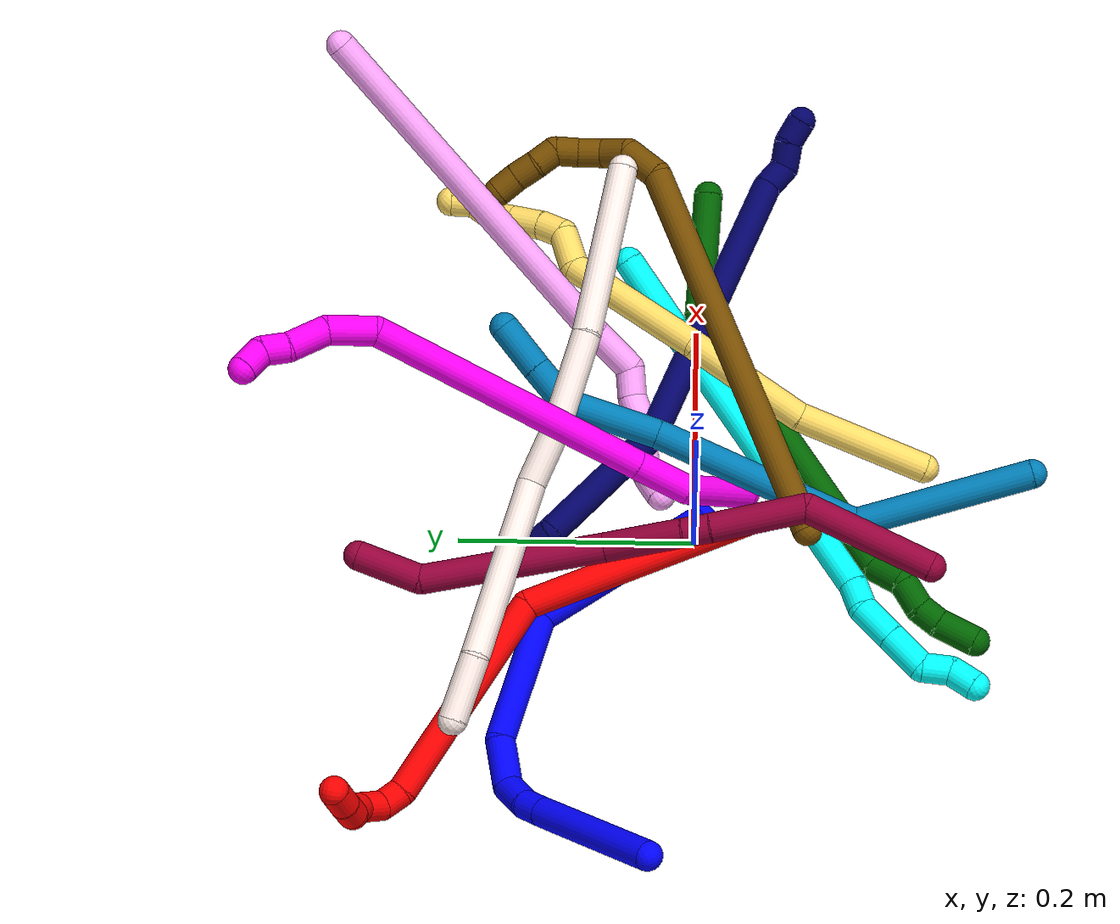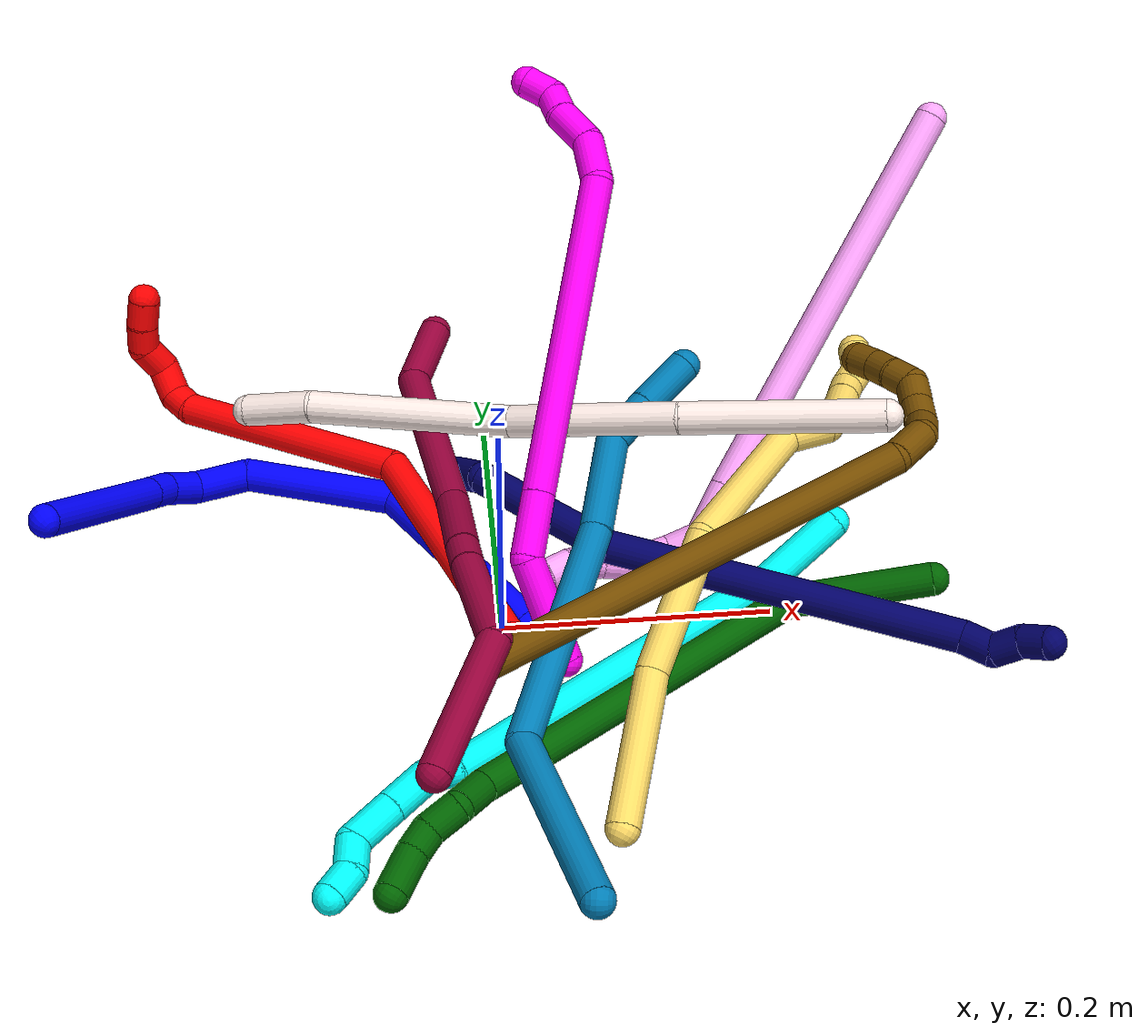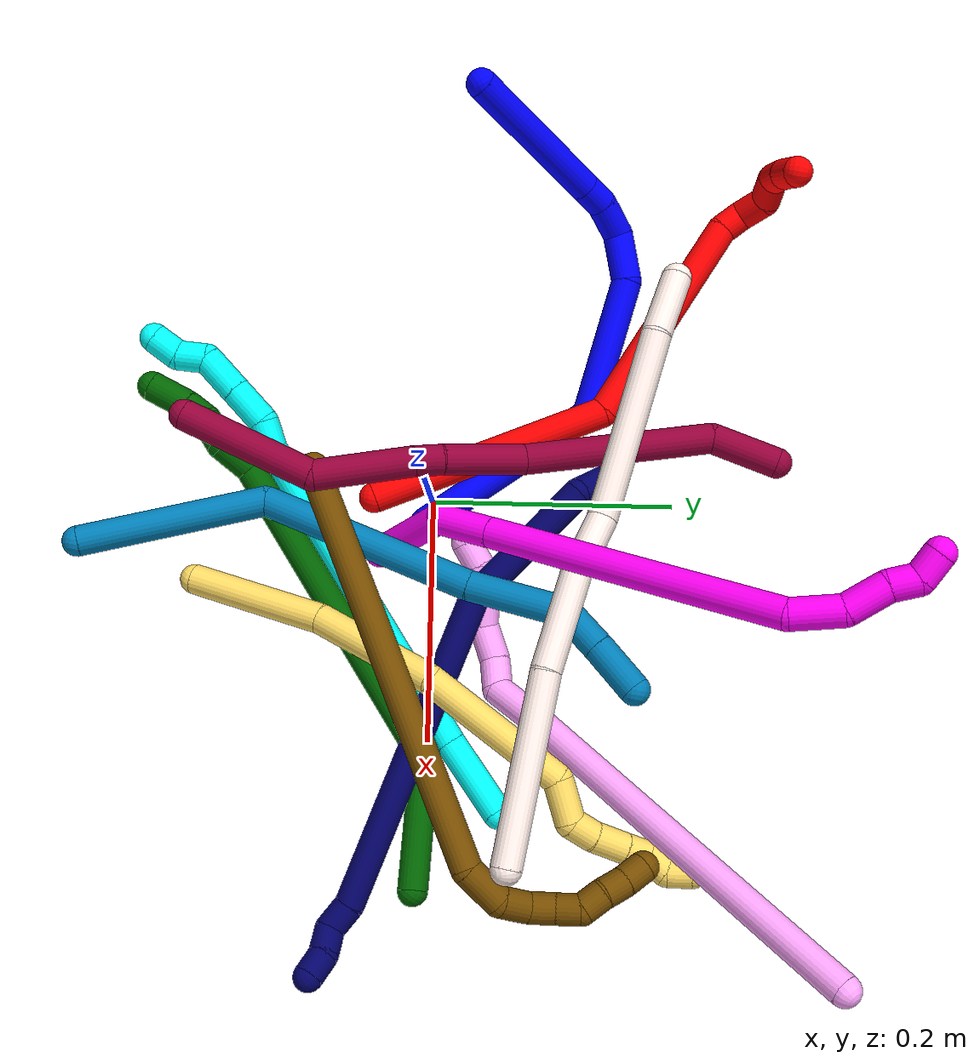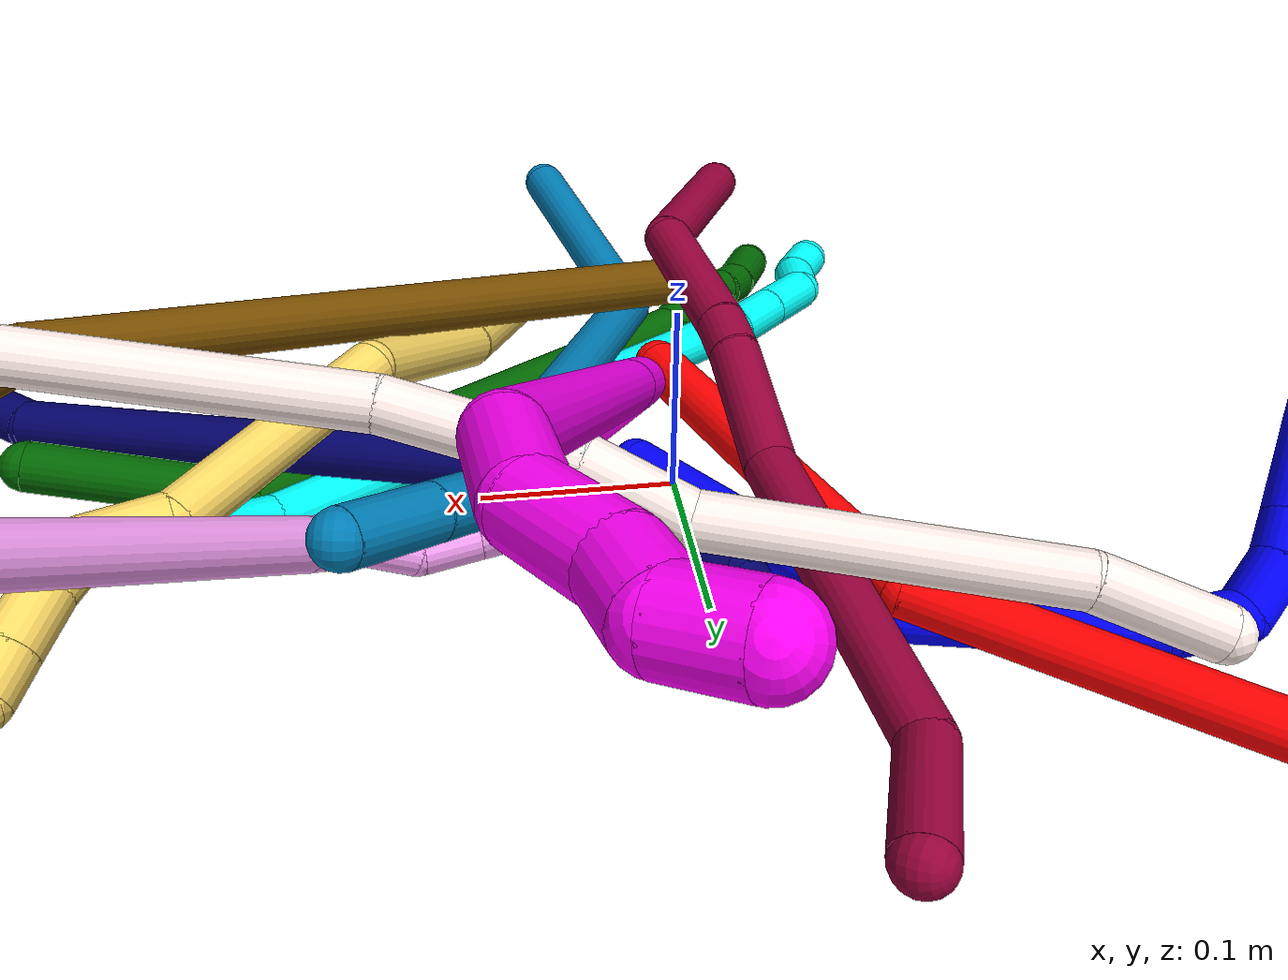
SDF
<sdf version="1.7">
 <world name="default">
  <plugin name="TubeGeneratorPlugin" filename="libtube_generator_plugin.so"/>
  <model name="photoneo_s_sensor">
   <static>1</static>
   <pose>0 0 2 1.57079 1.57079 3.14159</pose>
   <link name="link">
    <inertial><mass>0.1</mass></inertial>
    <sensor name="sensor" type="depth">
     <update_rate>30</update_rate>
     <camera>
      <horizontal_fov>1.22</horizontal_fov>
      <image><width>1920</width><height>1200</height><format>B8G8R8</format></image>
      <clip><near>0.1</near><far>4</far></clip>
      <depth_camera><output>points</output></depth_camera>
     </camera>
     <plugin name="camera_plugin" filename="libgazebo_ros_depth_camera.so">
      <baseline>0.2</baseline>
      <alwaysOn>1</alwaysOn>
      <updateRate>0.0</updateRate>
      <cameraName>camera_ir</cameraName>
      <imageTopicName>/camera/color/image_raw</imageTopicName>
      <cameraInfoTopicName>/camera/color/camera_info</cameraInfoTopicName>
      <depthImageTopicName>/camera/depth/image_raw</depthImageTopicName>
      <depthImageCameraInfoTopicName>/camera/depth/camera_info</depthImageCameraInfoTopicName>
      <pointCloudTopicName>/camera/depth/points</pointCloudTopicName>
      <frameName>fr_optical</frameName>
      <pointCloudCutoff>0.1</pointCloudCutoff>
      <pointCloudCutoffMax>2.0</pointCloudCutoffMax>
      <distortionK1>0</distortionK1>
      <distortionK2>0</distortionK2>
      <distortionK3>0</distortionK3>
      <distortionT1>0</distortionT1>
      <distortionT2>0</distortionT2>
      <CxPrime>0</CxPrime>
      <Cx>0</Cx>
      <Cy>0</Cy>
      <focalLength>0</focalLength>
      <hackBaseline>0</hackBaseline>
     </plugin>
    </sensor>
   </link>
  </model>
  <gravity>0 0 -9.8</gravity>
  <magnetic_field>6e-06 2.3e-05 -4.2e-05</magnetic_field>
  <atmosphere type="adiabatic"/>
  <physics name="default_physics" default="0" type="ode">
   <max_step_size>0.003</max_step_size>
   <real_time_factor>1</real_time_factor>
   <real_time_update_rate>1000</real_time_update_rate>
   <max_contacts>10000</max_contacts>
   <ode>
    <solver>
     <type>quick</type>
     <iters>100</iters>
     <sor>1.3</sor>
     <use_dynamic_moi_rescaling>0</use_dynamic_moi_rescaling>
    </solver>
    <constraints>
     <contact_max_correcting_vel>0</contact_max_correcting_vel>
     <contact_surface_layer>0.001</contact_surface_layer>
     <cfm>0</cfm>
     <erp>0.2</erp>
    </constraints>
   </ode>
  </physics>
  <scene><ambient>0.4 0.4 0.4 1</ambient><background>0.7 0.7 0.7 1</background><shadows>0</shadows></scene>
  <audio><device>default</device></audio>
  <spherical_coordinates>
   <surface_model>EARTH_WGS84</surface_model>
   <latitude_deg>0</latitude_deg>
   <longitude_deg>0</longitude_deg>
   <elevation>0</elevation>
   <heading_deg>0</heading_deg>
  </spherical_coordinates>
  <model name="bin">
   <static>1</static>
   <link name="bottom">
    <collision name="collision-bottom">
     <pose>0 0 -0.01 0 -0 0</pose>
     <geometry><box><size>0.8 0.6 0.02</size></box></geometry>
     <surface>
      <friction><ode><mu>100</mu><mu2>100</mu2></ode></friction>
      <contact><collide_bitmask>65535</collide_bitmask></contact>
     </surface>
    </collision>
   </link>
   <link name="west_wall">
    <collision name="collision-west_wall">
     <pose>-0.41 0 0.1 0 -0 0</pose>
     <geometry><box><size>0.02 0.6 0.2</size></box></geometry>
     <surface>
      <friction><ode><mu>100</mu><mu2>100</mu2></ode></friction>
      <contact><collide_bitmask>65535</collide_bitmask></contact>
     </surface>
    </collision>
   </link>
   <link name="east_wall">
    <collision name="collision-east_wall">
     <pose>0.41 0 0.1 0 -0 0</pose>
     <geometry><box><size>0.02 0.6 0.2</size></box></geometry>
     <surface>
      <friction><ode><mu>100</mu><mu2>100</mu2></ode></friction>
      <contact><collide_bitmask>65535</collide_bitmask></contact>
     </surface>
    </collision>
   </link>
   <link name="south_wall">
    <collision name="collision-south_wall">
     <pose>0 -0.31 0.1 0 -0 0</pose>
     <geometry><box><size>0.8 0.02 0.2</size></box></geometry>
     <surface>
      <friction><ode><mu>100</mu><mu2>100</mu2></ode></friction>
      <contact><collide_bitmask>65535</collide_bitmask></contact>
     </surface>
    </collision>
   </link>
   <link name="north_wall">
    <collision name="collision-north_wall">
     <pose>0 0.31 0.1 0 -0 0</pose>
     <geometry><box><size>0.8 0.02 0.2</size></box></geometry>
     <surface>
      <friction><ode><mu>100</mu><mu2>100</mu2></ode></friction>
      <contact><collide_bitmask>65535</collide_bitmask></contact>
     </surface>
    </collision>
   </link>
  </model>
  <model name="1">
   <static>0</static>
   <link name="1">
    <collision name="collision-cylinder-e_1_1_4">
     <pose>-0.004996 0.004509 0.081183 -0.055489 -0.061371 0.001704</pose>
     <geometry><cylinder><radius>0.0125</radius><length>0.162922</length></cylinder></geometry>
     <surface>
      <friction><ode><mu>1.16</mu><mu2>1.16</mu2><slip1>0</slip1><slip2>0</slip2></ode></friction>
      <contact><ode><kp>1e+06</kp><kd>1</kd><max_vel>0</max_vel><min_depth>0.001</min_depth></ode></contact>
     </surface>
    </collision>
    <visual name="visual-cylinder-e_1_1_4">
     <pose>-0.004996 0.004509 0.081183 -0.055489 -0.061371 0.001704</pose>
     <geometry><cylinder><radius>0.0125</radius><length>0.162922</length></cylinder></geometry>
     <material><ambient>0 0 1 1</ambient></material>
    </visual>
    <collision name="collision-cylinder-e_2_4_5">
     <pose>-0.048579 0.020546 0.204301 -0.268254 -0.725713 0.102373</pose>
     <geometry><cylinder><radius>0.0125</radius><length>0.116283</length></cylinder></geometry>
     <surface>
      <friction><ode><mu>1.16</mu><mu2>1.16</mu2><slip1>0</slip1><slip2>0</slip2></ode></friction>
      <contact><ode><kp>1e+06</kp><kd>1</kd><max_vel>0</max_vel><min_depth>0.001</min_depth></ode></contact>
     </surface>
    </collision>
    <visual name="visual-cylinder-e_2_4_5">
     <pose>-0.048579 0.020546 0.204301 -0.268254 -0.725713 0.102373</pose>
     <geometry><cylinder><radius>0.0125</radius><length>0.116283</length></cylinder></geometry>
     <material><ambient>0 0 1 1</ambient></material>
    </visual>
    <collision name="collision-cylinder-e_3_5_6">
     <pose>-0.105195 0.039379 0.25321 -0.808663 -1.06021 0.491422</pose>
     <geometry><cylinder><radius>0.0125</radius><length>0.041331</length></cylinder></geometry>
     <surface>
      <friction><ode><mu>1.16</mu><mu2>1.16</mu2><slip1>0</slip1><slip2>0</slip2></ode></friction>
      <contact><ode><kp>1e+06</kp><kd>1</kd><max_vel>0</max_vel><min_depth>0.001</min_depth></ode></contact>
     </surface>
    </collision>
    <visual name="visual-cylinder-e_3_5_6">
     <pose>-0.105195 0.039379 0.25321 -0.808663 -1.06021 0.491422</pose>
     <geometry><cylinder><radius>0.0125</radius><length>0.041331</length></cylinder></geometry>
     <material><ambient>0 0 1 1</ambient></material>
    </visual>
    <collision name="collision-cylinder-e_4_6_7">
     <pose>-0.138009 0.042701 0.259517 1.73658 -1.30417 -1.46768</pose>
     <geometry><cylinder><radius>0.0125</radius><length>0.030651</length></cylinder></geometry>
     <surface>
      <friction><ode><mu>1.16</mu><mu2>1.16</mu2><slip1>0</slip1><slip2>0</slip2></ode></friction>
      <contact><ode><kp>1e+06</kp><kd>1</kd><max_vel>0</max_vel><min_depth>0.001</min_depth></ode></contact>
     </surface>
    </collision>
    <visual name="visual-cylinder-e_4_6_7">
     <pose>-0.138009 0.042701 0.259517 1.73658 -1.30417 -1.46768</pose>
     <geometry><cylinder><radius>0.0125</radius><length>0.030651</length></cylinder></geometry>
     <material><ambient>0 0 1 1</ambient></material>
    </visual>
    <collision name="collision-cylinder-e_5_7_8">
     <pose>-0.162678 0.035785 0.255492 2.4236 -1.14702 -2.089</pose>
     <geometry><cylinder><radius>0.0125</radius><length>0.021689</length></cylinder></geometry>
     <surface>
      <friction><ode><mu>1.16</mu><mu2>1.16</mu2><slip1>0</slip1><slip2>0</slip2></ode></friction>
      <contact><ode><kp>1e+06</kp><kd>1</kd><max_vel>0</max_vel><min_depth>0.001</min_depth></ode></contact>
     </surface>
    </collision>
    <visual name="visual-cylinder-e_5_7_8">
     <pose>-0.162678 0.035785 0.255492 2.4236 -1.14702 -2.089</pose>
     <geometry><cylinder><radius>0.0125</radius><length>0.021689</length></cylinder></geometry>
     <material><ambient>0 0 1 1</ambient></material>
    </visual>
    <collision name="collision-cylinder-e_6_8_2">
     <pose>-0.229732 0.013565 0.232137 2.37428 -1.11844 -1.99594</pose>
     <geometry><cylinder><radius>0.0125</radius><length>0.127124</length></cylinder></geometry>
     <surface>
      <friction><ode><mu>1.16</mu><mu2>1.16</mu2><slip1>0</slip1><slip2>0</slip2></ode></friction>
      <contact><ode><kp>1e+06</kp><kd>1</kd><max_vel>0</max_vel><min_depth>0.001</min_depth></ode></contact>
     </surface>
    </collision>
    <visual name="visual-cylinder-e_6_8_2">
     <pose>-0.229732 0.013565 0.232137 2.37428 -1.11844 -1.99594</pose>
     <geometry><cylinder><radius>0.0125</radius><length>0.127124</length></cylinder></geometry>
     <material><ambient>0 0 1 1</ambient></material>
    </visual>
    <collision name="collision-sphere-2">
     <pose>-0.286901 -0.005722 0.21214 0 -0 0</pose>
     <geometry><sphere><radius>0.0125</radius></sphere></geometry>
     <surface>
      <friction><ode><mu>1.16</mu><mu2>1.16</mu2><slip1>0</slip1><slip2>0</slip2></ode></friction>
      <contact><ode><kp>1e+06</kp><kd>1</kd><max_vel>0</max_vel><min_depth>0.001</min_depth></ode></contact>
     </surface>
    </collision>
    <visual name="visual-sphere-2">
     <pose>-0.286901 -0.005722 0.21214 0 -0 0</pose>
     <geometry><sphere><radius>0.0125</radius></sphere></geometry>
     <material><ambient>0 0 1 1</ambient></material>
    </visual>
    <collision name="collision-sphere-4">
     <pose>-0.009992 0.009019 0.162365 0 -0 0</pose>
     <geometry><sphere><radius>0.0125</radius></sphere></geometry>
     <surface>
      <friction><ode><mu>1.16</mu><mu2>1.16</mu2><slip1>0</slip1><slip2>0</slip2></ode></friction>
      <contact><ode><kp>1e+06</kp><kd>1</kd><max_vel>0</max_vel><min_depth>0.001</min_depth></ode></contact>
     </surface>
    </collision>
    <visual name="visual-sphere-4">
     <pose>-0.009992 0.009019 0.162365 0 -0 0</pose>
     <geometry><sphere><radius>0.0125</radius></sphere></geometry>
     <material><ambient>0 0 1 1</ambient></material>
    </visual>
    <collision name="collision-sphere-1">
     <geometry><sphere><radius>0.0125</radius></sphere></geometry>
     <surface>
      <friction><ode><mu>1.16</mu><mu2>1.16</mu2><slip1>0</slip1><slip2>0</slip2></ode></friction>
      <contact><ode><kp>1e+06</kp><kd>1</kd><max_vel>0</max_vel><min_depth>0.001</min_depth></ode></contact>
     </surface>
    </collision>
    <visual name="visual-sphere-1">
     <geometry><sphere><radius>0.0125</radius></sphere></geometry>
     <material><ambient>0 0 1 1</ambient></material>
    </visual>
    <collision name="collision-sphere-8">
     <pose>-0.172564 0.032851 0.252133 0 -0 0</pose>
     <geometry><sphere><radius>0.0125</radius></sphere></geometry>
     <surface>
      <friction><ode><mu>1.16</mu><mu2>1.16</mu2><slip1>0</slip1><slip2>0</slip2></ode></friction>
      <contact><ode><kp>1e+06</kp><kd>1</kd><max_vel>0</max_vel><min_depth>0.001</min_depth></ode></contact>
     </surface>
    </collision>
    <visual name="visual-sphere-8">
     <pose>-0.172564 0.032851 0.252133 0 -0 0</pose>
     <geometry><sphere><radius>0.0125</radius></sphere></geometry>
     <material><ambient>0 0 1 1</ambient></material>
    </visual>
    <collision name="collision-sphere-5">
     <pose>-0.087166 0.032073 0.246237 0 -0 0</pose>
     <geometry><sphere><radius>0.0125</radius></sphere></geometry>
     <surface>
      <friction><ode><mu>1.16</mu><mu2>1.16</mu2><slip1>0</slip1><slip2>0</slip2></ode></friction>
      <contact><ode><kp>1e+06</kp><kd>1</kd><max_vel>0</max_vel><min_depth>0.001</min_depth></ode></contact>
     </surface>
    </collision>
    <visual name="visual-sphere-5">
     <pose>-0.087166 0.032073 0.246237 0 -0 0</pose>
     <geometry><sphere><radius>0.0125</radius></sphere></geometry>
     <material><ambient>0 0 1 1</ambient></material>
    </visual>
    <collision name="collision-sphere-6">
     <pose>-0.123225 0.046684 0.260183 0 -0 0</pose>
     <geometry><sphere><radius>0.0125</radius></sphere></geometry>
     <surface>
      <friction><ode><mu>1.16</mu><mu2>1.16</mu2><slip1>0</slip1><slip2>0</slip2></ode></friction>
      <contact><ode><kp>1e+06</kp><kd>1</kd><max_vel>0</max_vel><min_depth>0.001</min_depth></ode></contact>
     </surface>
    </collision>
    <visual name="visual-sphere-6">
     <pose>-0.123225 0.046684 0.260183 0 -0 0</pose>
     <geometry><sphere><radius>0.0125</radius></sphere></geometry>
     <material><ambient>0 0 1 1</ambient></material>
    </visual>
    <collision name="collision-sphere-7">
     <pose>-0.152793 0.038719 0.25885 0 -0 0</pose>
     <geometry><sphere><radius>0.0125</radius></sphere></geometry>
     <surface>
      <friction><ode><mu>1.16</mu><mu2>1.16</mu2><slip1>0</slip1><slip2>0</slip2></ode></friction>
      <contact><ode><kp>1e+06</kp><kd>1</kd><max_vel>0</max_vel><min_depth>0.001</min_depth></ode></contact>
     </surface>
    </collision>
    <visual name="visual-sphere-7">
     <pose>-0.152793 0.038719 0.25885 0 -0 0</pose>
     <geometry><sphere><radius>0.0125</radius></sphere></geometry>
     <material><ambient>0 0 1 1</ambient></material>
    </visual>
    <inertial>
     <pose>-0.095547 0.017122 0.180909 0 -0 0</pose>
     <mass>0.5</mass>
     <inertia>
      <ixx>0.000357</ixx>
      <ixy>0</ixy>
      <ixz>0</ixz>
      <iyy>0.000603</iyy>
      <iyz>0</iyz>
      <izz>0.000304</izz>
     </inertia>
    </inertial>
   </link>
   <pose>0.018815 -0.005978 0.011493 -1.53435 0.300577 0.547363</pose>
  </model>
  <model name="2">
   <static>0</static>
   <link name="2">
    <collision name="collision-cylinder-e_1_1_4">
     <pose>-0.027704 0.045002 0.084976 -0.487036 -0.280519 0.070126</pose>
     <geometry><cylinder><radius>0.0125</radius><length>0.200136</length></cylinder></geometry>
     <surface>
      <friction><ode><mu>1.16</mu><mu2>1.16</mu2><slip1>0</slip1><slip2>0</slip2></ode></friction>
      <contact><ode><kp>1e+06</kp><kd>1</kd><max_vel>0</max_vel><min_depth>0.001</min_depth></ode></contact>
     </surface>
    </collision>
    <visual name="visual-cylinder-e_1_1_4">
     <pose>-0.027704 0.045002 0.084976 -0.487036 -0.280519 0.070126</pose>
     <geometry><cylinder><radius>0.0125</radius><length>0.200136</length></cylinder></geometry>
     <material><ambient>1 0 0 1</ambient></material>
    </visual>
    <collision name="collision-cylinder-e_2_4_5">
     <pose>-0.101498 0.164231 0.205125 -1.12828 -0.511342 0.327814</pose>
     <geometry><cylinder><radius>0.0125</radius><length>0.188374</length></cylinder></geometry>
     <surface>
      <friction><ode><mu>1.16</mu><mu2>1.16</mu2><slip1>0</slip1><slip2>0</slip2></ode></friction>
      <contact><ode><kp>1e+06</kp><kd>1</kd><max_vel>0</max_vel><min_depth>0.001</min_depth></ode></contact>
     </surface>
    </collision>
    <visual name="visual-cylinder-e_2_4_5">
     <pose>-0.101498 0.164231 0.205125 -1.12828 -0.511342 0.327814</pose>
     <geometry><cylinder><radius>0.0125</radius><length>0.188374</length></cylinder></geometry>
     <material><ambient>1 0 0 1</ambient></material>
    </visual>
    <collision name="collision-cylinder-e_3_5_6">
     <pose>-0.152165 0.244524 0.247315 -0.712796 -0.458345 0.173257</pose>
     <geometry><cylinder><radius>0.0125</radius><length>0.020685</length></cylinder></geometry>
     <surface>
      <friction><ode><mu>1.16</mu><mu2>1.16</mu2><slip1>0</slip1><slip2>0</slip2></ode></friction>
      <contact><ode><kp>1e+06</kp><kd>1</kd><max_vel>0</max_vel><min_depth>0.001</min_depth></ode></contact>
     </surface>
    </collision>
    <visual name="visual-cylinder-e_3_5_6">
     <pose>-0.152165 0.244524 0.247315 -0.712796 -0.458345 0.173257</pose>
     <geometry><cylinder><radius>0.0125</radius><length>0.020685</length></cylinder></geometry>
     <material><ambient>1 0 0 1</ambient></material>
    </visual>
    <collision name="collision-cylinder-e_4_6_7">
     <pose>-0.166487 0.249707 0.262303 0.110255 -0.882244 -0.052098</pose>
     <geometry><cylinder><radius>0.0125</radius><length>0.025244</length></cylinder></geometry>
     <surface>
      <friction><ode><mu>1.16</mu><mu2>1.16</mu2><slip1>0</slip1><slip2>0</slip2></ode></friction>
      <contact><ode><kp>1e+06</kp><kd>1</kd><max_vel>0</max_vel><min_depth>0.001</min_depth></ode></contact>
     </surface>
    </collision>
    <visual name="visual-cylinder-e_4_6_7">
     <pose>-0.166487 0.249707 0.262303 0.110255 -0.882244 -0.052098</pose>
     <geometry><cylinder><radius>0.0125</radius><length>0.025244</length></cylinder></geometry>
     <material><ambient>1 0 0 1</ambient></material>
    </visual>
    <collision name="collision-cylinder-e_5_7_8">
     <pose>-0.188007 0.248131 0.270973 0.782014 -1.48737 -0.724895</pose>
     <geometry><cylinder><radius>0.0125</radius><length>0.02363</length></cylinder></geometry>
     <surface>
      <friction><ode><mu>1.16</mu><mu2>1.16</mu2><slip1>0</slip1><slip2>0</slip2></ode></friction>
      <contact><ode><kp>1e+06</kp><kd>1</kd><max_vel>0</max_vel><min_depth>0.001</min_depth></ode></contact>
     </surface>
    </collision>
    <visual name="visual-cylinder-e_5_7_8">
     <pose>-0.188007 0.248131 0.270973 0.782014 -1.48737 -0.724895</pose>
     <geometry><cylinder><radius>0.0125</radius><length>0.02363</length></cylinder></geometry>
     <material><ambient>1 0 0 1</ambient></material>
    </visual>
    <collision name="collision-cylinder-e_6_8_9">
     <pose>-0.207148 0.241303 0.274686 1.11409 -0.822869 -0.530721</pose>
     <geometry><cylinder><radius>0.0125</radius><length>0.020097</length></cylinder></geometry>
     <surface>
      <friction><ode><mu>1.16</mu><mu2>1.16</mu2><slip1>0</slip1><slip2>0</slip2></ode></friction>
      <contact><ode><kp>1e+06</kp><kd>1</kd><max_vel>0</max_vel><min_depth>0.001</min_depth></ode></contact>
     </surface>
    </collision>
    <visual name="visual-cylinder-e_6_8_9">
     <pose>-0.207148 0.241303 0.274686 1.11409 -0.822869 -0.530721</pose>
     <geometry><cylinder><radius>0.0125</radius><length>0.020097</length></cylinder></geometry>
     <material><ambient>1 0 0 1</ambient></material>
    </visual>
    <collision name="collision-cylinder-e_7_9_2">
     <pose>-0.221535 0.22785 0.281741 1.06626 -0.698459 -0.423357</pose>
     <geometry><cylinder><radius>0.0125</radius><length>0.021835</length></cylinder></geometry>
     <surface>
      <friction><ode><mu>1.16</mu><mu2>1.16</mu2><slip1>0</slip1><slip2>0</slip2></ode></friction>
      <contact><ode><kp>1e+06</kp><kd>1</kd><max_vel>0</max_vel><min_depth>0.001</min_depth></ode></contact>
     </surface>
    </collision>
    <visual name="visual-cylinder-e_7_9_2">
     <pose>-0.221535 0.22785 0.281741 1.06626 -0.698459 -0.423357</pose>
     <geometry><cylinder><radius>0.0125</radius><length>0.021835</length></cylinder></geometry>
     <material><ambient>1 0 0 1</ambient></material>
    </visual>
    <collision name="collision-sphere-2">
     <pose>-0.228555 0.220531 0.285783 0 -0 0</pose>
     <geometry><sphere><radius>0.0125</radius></sphere></geometry>
     <surface>
      <friction><ode><mu>1.16</mu><mu2>1.16</mu2><slip1>0</slip1><slip2>0</slip2></ode></friction>
      <contact><ode><kp>1e+06</kp><kd>1</kd><max_vel>0</max_vel><min_depth>0.001</min_depth></ode></contact>
     </surface>
    </collision>
    <visual name="visual-sphere-2">
     <pose>-0.228555 0.220531 0.285783 0 -0 0</pose>
     <geometry><sphere><radius>0.0125</radius></sphere></geometry>
     <material><ambient>1 0 0 1</ambient></material>
    </visual>
    <collision name="collision-sphere-9">
     <pose>-0.214515 0.235169 0.2777 0 -0 0</pose>
     <geometry><sphere><radius>0.0125</radius></sphere></geometry>
     <surface>
      <friction><ode><mu>1.16</mu><mu2>1.16</mu2><slip1>0</slip1><slip2>0</slip2></ode></friction>
      <contact><ode><kp>1e+06</kp><kd>1</kd><max_vel>0</max_vel><min_depth>0.001</min_depth></ode></contact>
     </surface>
    </collision>
    <visual name="visual-sphere-9">
     <pose>-0.214515 0.235169 0.2777 0 -0 0</pose>
     <geometry><sphere><radius>0.0125</radius></sphere></geometry>
     <material><ambient>1 0 0 1</ambient></material>
    </visual>
    <collision name="collision-sphere-4">
     <pose>-0.055408 0.090004 0.169951 0 -0 0</pose>
     <geometry><sphere><radius>0.0125</radius></sphere></geometry>
     <surface>
      <friction><ode><mu>1.16</mu><mu2>1.16</mu2><slip1>0</slip1><slip2>0</slip2></ode></friction>
      <contact><ode><kp>1e+06</kp><kd>1</kd><max_vel>0</max_vel><min_depth>0.001</min_depth></ode></contact>
     </surface>
    </collision>
    <visual name="visual-sphere-4">
     <pose>-0.055408 0.090004 0.169951 0 -0 0</pose>
     <geometry><sphere><radius>0.0125</radius></sphere></geometry>
     <material><ambient>1 0 0 1</ambient></material>
    </visual>
    <collision name="collision-sphere-1">
     <geometry><sphere><radius>0.0125</radius></sphere></geometry>
     <surface>
      <friction><ode><mu>1.16</mu><mu2>1.16</mu2><slip1>0</slip1><slip2>0</slip2></ode></friction>
      <contact><ode><kp>1e+06</kp><kd>1</kd><max_vel>0</max_vel><min_depth>0.001</min_depth></ode></contact>
     </surface>
    </collision>
    <visual name="visual-sphere-1">
     <geometry><sphere><radius>0.0125</radius></sphere></geometry>
     <material><ambient>1 0 0 1</ambient></material>
    </visual>
    <collision name="collision-sphere-8">
     <pose>-0.199781 0.247437 0.271672 0 -0 0</pose>
     <geometry><sphere><radius>0.0125</radius></sphere></geometry>
     <surface>
      <friction><ode><mu>1.16</mu><mu2>1.16</mu2><slip1>0</slip1><slip2>0</slip2></ode></friction>
      <contact><ode><kp>1e+06</kp><kd>1</kd><max_vel>0</max_vel><min_depth>0.001</min_depth></ode></contact>
     </surface>
    </collision>
    <visual name="visual-sphere-8">
     <pose>-0.199781 0.247437 0.271672 0 -0 0</pose>
     <geometry><sphere><radius>0.0125</radius></sphere></geometry>
     <material><ambient>1 0 0 1</ambient></material>
    </visual>
    <collision name="collision-sphere-5">
     <pose>-0.147589 0.238459 0.240298 0 -0 0</pose>
     <geometry><sphere><radius>0.0125</radius></sphere></geometry>
     <surface>
      <friction><ode><mu>1.16</mu><mu2>1.16</mu2><slip1>0</slip1><slip2>0</slip2></ode></friction>
      <contact><ode><kp>1e+06</kp><kd>1</kd><max_vel>0</max_vel><min_depth>0.001</min_depth></ode></contact>
     </surface>
    </collision>
    <visual name="visual-sphere-5">
     <pose>-0.147589 0.238459 0.240298 0 -0 0</pose>
     <geometry><sphere><radius>0.0125</radius></sphere></geometry>
     <material><ambient>1 0 0 1</ambient></material>
    </visual>
    <collision name="collision-sphere-6">
     <pose>-0.156741 0.250589 0.254331 0 -0 0</pose>
     <geometry><sphere><radius>0.0125</radius></sphere></geometry>
     <surface>
      <friction><ode><mu>1.16</mu><mu2>1.16</mu2><slip1>0</slip1><slip2>0</slip2></ode></friction>
      <contact><ode><kp>1e+06</kp><kd>1</kd><max_vel>0</max_vel><min_depth>0.001</min_depth></ode></contact>
     </surface>
    </collision>
    <visual name="visual-sphere-6">
     <pose>-0.156741 0.250589 0.254331 0 -0 0</pose>
     <geometry><sphere><radius>0.0125</radius></sphere></geometry>
     <material><ambient>1 0 0 1</ambient></material>
    </visual>
    <collision name="collision-sphere-7">
     <pose>-0.176234 0.248824 0.270275 0 -0 0</pose>
     <geometry><sphere><radius>0.0125</radius></sphere></geometry>
     <surface>
      <friction><ode><mu>1.16</mu><mu2>1.16</mu2><slip1>0</slip1><slip2>0</slip2></ode></friction>
      <contact><ode><kp>1e+06</kp><kd>1</kd><max_vel>0</max_vel><min_depth>0.001</min_depth></ode></contact>
     </surface>
    </collision>
    <visual name="visual-sphere-7">
     <pose>-0.176234 0.248824 0.270275 0 -0 0</pose>
     <geometry><sphere><radius>0.0125</radius></sphere></geometry>
     <material><ambient>1 0 0 1</ambient></material>
    </visual>
    <inertial>
     <pose>-0.090915 0.133986 0.170918 0 -0 0</pose>
     <mass>0.5</mass>
     <inertia>
      <ixx>0.001304</ixx>
      <ixy>0</ixy>
      <ixz>0</ixz>
      <iyy>0.001139</iyy>
      <iyz>0</iyz>
      <izz>-0.000255</izz>
     </inertia>
    </inertial>
   </link>
   <pose>0.001478 -0.045863 0.047006 -1.54454 0.879819 -0.145023</pose>
  </model>
  <model name="3">
   <static>0</static>
   <link name="3">
    <collision name="collision-cylinder-e_1_1_4">
     <pose>-0.024623 -0.022757 0.010895 1.12429 -0.773227 -0.502079</pose>
     <geometry><cylinder><radius>0.0125</radius><length>0.070508</length></cylinder></geometry>
     <surface>
      <friction><ode><mu>1.16</mu><mu2>1.16</mu2><slip1>0</slip1><slip2>0</slip2></ode></friction>
      <contact><ode><kp>1e+06</kp><kd>1</kd><max_vel>0</max_vel><min_depth>0.001</min_depth></ode></contact>
     </surface>
    </collision>
    <visual name="visual-cylinder-e_1_1_4">
     <pose>-0.024623 -0.022757 0.010895 1.12429 -0.773227 -0.502079</pose>
     <geometry><cylinder><radius>0.0125</radius><length>0.070508</length></cylinder></geometry>
     <material><ambient>0.003922 1 0.996078 1</ambient></material>
    </visual>
    <collision name="collision-cylinder-e_2_4_5">
     <pose>-0.158016 -0.111144 0.086388 0.793329 -0.868251 -0.383618</pose>
     <geometry><cylinder><radius>0.0125</radius><length>0.285034</length></cylinder></geometry>
     <surface>
      <friction><ode><mu>1.16</mu><mu2>1.16</mu2><slip1>0</slip1><slip2>0</slip2></ode></friction>
      <contact><ode><kp>1e+06</kp><kd>1</kd><max_vel>0</max_vel><min_depth>0.001</min_depth></ode></contact>
     </surface>
    </collision>
    <visual name="visual-cylinder-e_2_4_5">
     <pose>-0.158016 -0.111144 0.086388 0.793329 -0.868251 -0.383618</pose>
     <geometry><cylinder><radius>0.0125</radius><length>0.285034</length></cylinder></geometry>
     <material><ambient>0.003922 1 0.996078 1</ambient></material>
    </visual>
    <collision name="collision-cylinder-e_3_5_6">
     <pose>-0.277542 -0.17974 0.155494 0.581822 -1.10595 -0.365465</pose>
     <geometry><cylinder><radius>0.0125</radius><length>0.024068</length></cylinder></geometry>
     <surface>
      <friction><ode><mu>1.16</mu><mu2>1.16</mu2><slip1>0</slip1><slip2>0</slip2></ode></friction>
      <contact><ode><kp>1e+06</kp><kd>1</kd><max_vel>0</max_vel><min_depth>0.001</min_depth></ode></contact>
     </surface>
    </collision>
    <visual name="visual-cylinder-e_3_5_6">
     <pose>-0.277542 -0.17974 0.155494 0.581822 -1.10595 -0.365465</pose>
     <geometry><cylinder><radius>0.0125</radius><length>0.024068</length></cylinder></geometry>
     <material><ambient>0.003922 1 0.996078 1</ambient></material>
    </visual>
    <collision name="collision-cylinder-e_4_6_7">
     <pose>-0.299281 -0.192443 0.169395 0.803389 -0.681787 -0.299133</pose>
     <geometry><cylinder><radius>0.0125</radius><length>0.034853</length></cylinder></geometry>
     <surface>
      <friction><ode><mu>1.16</mu><mu2>1.16</mu2><slip1>0</slip1><slip2>0</slip2></ode></friction>
      <contact><ode><kp>1e+06</kp><kd>1</kd><max_vel>0</max_vel><min_depth>0.001</min_depth></ode></contact>
     </surface>
    </collision>
    <visual name="visual-cylinder-e_4_6_7">
     <pose>-0.299281 -0.192443 0.169395 0.803389 -0.681787 -0.299133</pose>
     <geometry><cylinder><radius>0.0125</radius><length>0.034853</length></cylinder></geometry>
     <material><ambient>0.003922 1 0.996078 1</ambient></material>
    </visual>
    <collision name="collision-cylinder-e_5_7_8">
     <pose>-0.321867 -0.212575 0.188661 0.811158 -0.680505 -0.301713</pose>
     <geometry><cylinder><radius>0.0125</radius><length>0.036885</length></cylinder></geometry>
     <surface>
      <friction><ode><mu>1.16</mu><mu2>1.16</mu2><slip1>0</slip1><slip2>0</slip2></ode></friction>
      <contact><ode><kp>1e+06</kp><kd>1</kd><max_vel>0</max_vel><min_depth>0.001</min_depth></ode></contact>
     </surface>
    </collision>
    <visual name="visual-cylinder-e_5_7_8">
     <pose>-0.321867 -0.212575 0.188661 0.811158 -0.680505 -0.301713</pose>
     <geometry><cylinder><radius>0.0125</radius><length>0.036885</length></cylinder></geometry>
     <material><ambient>0.003922 1 0.996078 1</ambient></material>
    </visual>
    <collision name="collision-cylinder-e_6_8_9">
     <pose>-0.333058 -0.231699 0.207286 0.784062 0.033322 0.013778</pose>
     <geometry><cylinder><radius>0.0125</radius><length>0.02474</length></cylinder></geometry>
     <surface>
      <friction><ode><mu>1.16</mu><mu2>1.16</mu2><slip1>0</slip1><slip2>0</slip2></ode></friction>
      <contact><ode><kp>1e+06</kp><kd>1</kd><max_vel>0</max_vel><min_depth>0.001</min_depth></ode></contact>
     </surface>
    </collision>
    <visual name="visual-cylinder-e_6_8_9">
     <pose>-0.333058 -0.231699 0.207286 0.784062 0.033322 0.013778</pose>
     <geometry><cylinder><radius>0.0125</radius><length>0.02474</length></cylinder></geometry>
     <material><ambient>0.003922 1 0.996078 1</ambient></material>
    </visual>
    <collision name="collision-cylinder-e_7_9_2">
     <pose>-0.338218 -0.24729 0.22409 0.70577 -0.484834 -0.181646</pose>
     <geometry><cylinder><radius>0.0125</radius><length>0.023911</length></cylinder></geometry>
     <surface>
      <friction><ode><mu>1.16</mu><mu2>1.16</mu2><slip1>0</slip1><slip2>0</slip2></ode></friction>
      <contact><ode><kp>1e+06</kp><kd>1</kd><max_vel>0</max_vel><min_depth>0.001</min_depth></ode></contact>
     </surface>
    </collision>
    <visual name="visual-cylinder-e_7_9_2">
     <pose>-0.338218 -0.24729 0.22409 0.70577 -0.484834 -0.181646</pose>
     <geometry><cylinder><radius>0.0125</radius><length>0.023911</length></cylinder></geometry>
     <material><ambient>0.003922 1 0.996078 1</ambient></material>
    </visual>
    <collision name="collision-sphere-2">
     <pose>-0.34379 -0.254151 0.232141 0 -0 0</pose>
     <geometry><sphere><radius>0.0125</radius></sphere></geometry>
     <surface>
      <friction><ode><mu>1.16</mu><mu2>1.16</mu2><slip1>0</slip1><slip2>0</slip2></ode></friction>
      <contact><ode><kp>1e+06</kp><kd>1</kd><max_vel>0</max_vel><min_depth>0.001</min_depth></ode></contact>
     </surface>
    </collision>
    <visual name="visual-sphere-2">
     <pose>-0.34379 -0.254151 0.232141 0 -0 0</pose>
     <geometry><sphere><radius>0.0125</radius></sphere></geometry>
     <material><ambient>0.003922 1 0.996078 1</ambient></material>
    </visual>
    <collision name="collision-sphere-9">
     <pose>-0.332646 -0.24043 0.21604 0 -0 0</pose>
     <geometry><sphere><radius>0.0125</radius></sphere></geometry>
     <surface>
      <friction><ode><mu>1.16</mu><mu2>1.16</mu2><slip1>0</slip1><slip2>0</slip2></ode></friction>
      <contact><ode><kp>1e+06</kp><kd>1</kd><max_vel>0</max_vel><min_depth>0.001</min_depth></ode></contact>
     </surface>
    </collision>
    <visual name="visual-sphere-9">
     <pose>-0.332646 -0.24043 0.21604 0 -0 0</pose>
     <geometry><sphere><radius>0.0125</radius></sphere></geometry>
     <material><ambient>0.003922 1 0.996078 1</ambient></material>
    </visual>
    <collision name="collision-sphere-4">
     <pose>-0.049247 -0.045513 0.02179 0 -0 0</pose>
     <geometry><sphere><radius>0.0125</radius></sphere></geometry>
     <surface>
      <friction><ode><mu>1.16</mu><mu2>1.16</mu2><slip1>0</slip1><slip2>0</slip2></ode></friction>
      <contact><ode><kp>1e+06</kp><kd>1</kd><max_vel>0</max_vel><min_depth>0.001</min_depth></ode></contact>
     </surface>
    </collision>
    <visual name="visual-sphere-4">
     <pose>-0.049247 -0.045513 0.02179 0 -0 0</pose>
     <geometry><sphere><radius>0.0125</radius></sphere></geometry>
     <material><ambient>0.003922 1 0.996078 1</ambient></material>
    </visual>
    <collision name="collision-sphere-1">
     <geometry><sphere><radius>0.0125</radius></sphere></geometry>
     <surface>
      <friction><ode><mu>1.16</mu><mu2>1.16</mu2><slip1>0</slip1><slip2>0</slip2></ode></friction>
      <contact><ode><kp>1e+06</kp><kd>1</kd><max_vel>0</max_vel><min_depth>0.001</min_depth></ode></contact>
     </surface>
    </collision>
    <visual name="visual-sphere-1">
     <geometry><sphere><radius>0.0125</radius></sphere></geometry>
     <material><ambient>0.003922 1 0.996078 1</ambient></material>
    </visual>
    <collision name="collision-sphere-8">
     <pose>-0.333471 -0.222969 0.198532 0 -0 0</pose>
     <geometry><sphere><radius>0.0125</radius></sphere></geometry>
     <surface>
      <friction><ode><mu>1.16</mu><mu2>1.16</mu2><slip1>0</slip1><slip2>0</slip2></ode></friction>
      <contact><ode><kp>1e+06</kp><kd>1</kd><max_vel>0</max_vel><min_depth>0.001</min_depth></ode></contact>
     </surface>
    </collision>
    <visual name="visual-sphere-8">
     <pose>-0.333471 -0.222969 0.198532 0 -0 0</pose>
     <geometry><sphere><radius>0.0125</radius></sphere></geometry>
     <material><ambient>0.003922 1 0.996078 1</ambient></material>
    </visual>
    <collision name="collision-sphere-5">
     <pose>-0.266785 -0.176776 0.150987 0 -0 0</pose>
     <geometry><sphere><radius>0.0125</radius></sphere></geometry>
     <surface>
      <friction><ode><mu>1.16</mu><mu2>1.16</mu2><slip1>0</slip1><slip2>0</slip2></ode></friction>
      <contact><ode><kp>1e+06</kp><kd>1</kd><max_vel>0</max_vel><min_depth>0.001</min_depth></ode></contact>
     </surface>
    </collision>
    <visual name="visual-sphere-5">
     <pose>-0.266785 -0.176776 0.150987 0 -0 0</pose>
     <geometry><sphere><radius>0.0125</radius></sphere></geometry>
     <material><ambient>0.003922 1 0.996078 1</ambient></material>
    </visual>
    <collision name="collision-sphere-6">
     <pose>-0.288299 -0.182705 0.160001 0 -0 0</pose>
     <geometry><sphere><radius>0.0125</radius></sphere></geometry>
     <surface>
      <friction><ode><mu>1.16</mu><mu2>1.16</mu2><slip1>0</slip1><slip2>0</slip2></ode></friction>
      <contact><ode><kp>1e+06</kp><kd>1</kd><max_vel>0</max_vel><min_depth>0.001</min_depth></ode></contact>
     </surface>
    </collision>
    <visual name="visual-sphere-6">
     <pose>-0.288299 -0.182705 0.160001 0 -0 0</pose>
     <geometry><sphere><radius>0.0125</radius></sphere></geometry>
     <material><ambient>0.003922 1 0.996078 1</ambient></material>
    </visual>
    <collision name="collision-sphere-7">
     <pose>-0.310263 -0.202182 0.178789 0 -0 0</pose>
     <geometry><sphere><radius>0.0125</radius></sphere></geometry>
     <surface>
      <friction><ode><mu>1.16</mu><mu2>1.16</mu2><slip1>0</slip1><slip2>0</slip2></ode></friction>
      <contact><ode><kp>1e+06</kp><kd>1</kd><max_vel>0</max_vel><min_depth>0.001</min_depth></ode></contact>
     </surface>
    </collision>
    <visual name="visual-sphere-7">
     <pose>-0.310263 -0.202182 0.178789 0 -0 0</pose>
     <geometry><sphere><radius>0.0125</radius></sphere></geometry>
     <material><ambient>0.003922 1 0.996078 1</ambient></material>
    </visual>
    <inertial>
     <pose>-0.184172 -0.127607 0.104967 0 -0 0</pose>
     <mass>0.5</mass>
     <inertia>
      <ixx>0.000685</ixx>
      <ixy>0</ixy>
      <ixz>0</ixz>
      <iyy>0.00119</iyy>
      <iyz>0</iyz>
      <izz>0.002455</izz>
     </inertia>
    </inertial>
   </link>
   <pose>0.255427 0.059848 0.028089 0.812248 0.029429 -0.13285</pose>
  </model>
  <model name="4">
   <static>0</static>
   <link name="4">
    <collision name="collision-cylinder-e_1_1_4">
     <pose>0.010933 -0.008505 -0.163945 3.08976 0.066501 1.81768</pose>
     <geometry><cylinder><radius>0.0125</radius><length>0.329058</length></cylinder></geometry>
     <surface>
      <friction><ode><mu>1.16</mu><mu2>1.16</mu2><slip1>0</slip1><slip2>0</slip2></ode></friction>
      <contact><ode><kp>1e+06</kp><kd>1</kd><max_vel>0</max_vel><min_depth>0.001</min_depth></ode></contact>
     </surface>
    </collision>
    <visual name="visual-cylinder-e_1_1_4">
     <pose>0.010933 -0.008505 -0.163945 3.08976 0.066501 1.81768</pose>
     <geometry><cylinder><radius>0.0125</radius><length>0.329058</length></cylinder></geometry>
     <material><ambient>1 0.65098 0.996078 1</ambient></material>
    </visual>
    <collision name="collision-cylinder-e_2_4_5">
     <pose>0.023827 -0.019169 -0.348842 3.03885 0.092814 1.46914</pose>
     <geometry><cylinder><radius>0.0125</radius><length>0.042309</length></cylinder></geometry>
     <surface>
      <friction><ode><mu>1.16</mu><mu2>1.16</mu2><slip1>0</slip1><slip2>0</slip2></ode></friction>
      <contact><ode><kp>1e+06</kp><kd>1</kd><max_vel>0</max_vel><min_depth>0.001</min_depth></ode></contact>
     </surface>
    </collision>
    <visual name="visual-cylinder-e_2_4_5">
     <pose>0.023827 -0.019169 -0.348842 3.03885 0.092814 1.46914</pose>
     <geometry><cylinder><radius>0.0125</radius><length>0.042309</length></cylinder></geometry>
     <material><ambient>1 0.65098 0.996078 1</ambient></material>
    </visual>
    <collision name="collision-cylinder-e_3_5_6">
     <pose>0.020549 -0.015917 -0.380524 -2.67437 -0.411053 1.43889</pose>
     <geometry><cylinder><radius>0.0125</radius><length>0.02622</length></cylinder></geometry>
     <surface>
      <friction><ode><mu>1.16</mu><mu2>1.16</mu2><slip1>0</slip1><slip2>0</slip2></ode></friction>
      <contact><ode><kp>1e+06</kp><kd>1</kd><max_vel>0</max_vel><min_depth>0.001</min_depth></ode></contact>
     </surface>
    </collision>
    <visual name="visual-cylinder-e_3_5_6">
     <pose>0.020549 -0.015917 -0.380524 -2.67437 -0.411053 1.43889</pose>
     <geometry><cylinder><radius>0.0125</radius><length>0.02622</length></cylinder></geometry>
     <material><ambient>1 0.65098 0.996078 1</ambient></material>
    </visual>
    <collision name="collision-cylinder-e_4_6_7">
     <pose>0.006178 -0.010008 -0.403276 -3.10039 -0.649236 3.0193</pose>
     <geometry><cylinder><radius>0.0125</radius><length>0.030211</length></cylinder></geometry>
     <surface>
      <friction><ode><mu>1.16</mu><mu2>1.16</mu2><slip1>0</slip1><slip2>0</slip2></ode></friction>
      <contact><ode><kp>1e+06</kp><kd>1</kd><max_vel>0</max_vel><min_depth>0.001</min_depth></ode></contact>
     </surface>
    </collision>
    <visual name="visual-cylinder-e_4_6_7">
     <pose>0.006178 -0.010008 -0.403276 -3.10039 -0.649236 3.0193</pose>
     <geometry><cylinder><radius>0.0125</radius><length>0.030211</length></cylinder></geometry>
     <material><ambient>1 0.65098 0.996078 1</ambient></material>
    </visual>
    <collision name="collision-cylinder-e_5_7_8">
     <pose>-0.013529 -0.00768 -0.421255 -2.8431 -1.03823 2.62695</pose>
     <geometry><cylinder><radius>0.0125</radius><length>0.024549</length></cylinder></geometry>
     <surface>
      <friction><ode><mu>1.16</mu><mu2>1.16</mu2><slip1>0</slip1><slip2>0</slip2></ode></friction>
      <contact><ode><kp>1e+06</kp><kd>1</kd><max_vel>0</max_vel><min_depth>0.001</min_depth></ode></contact>
     </surface>
    </collision>
    <visual name="visual-cylinder-e_5_7_8">
     <pose>-0.013529 -0.00768 -0.421255 -2.8431 -1.03823 2.62695</pose>
     <geometry><cylinder><radius>0.0125</radius><length>0.024549</length></cylinder></geometry>
     <material><ambient>1 0.65098 0.996078 1</ambient></material>
    </visual>
    <collision name="collision-cylinder-e_6_8_9">
     <pose>-0.034067 -0.004912 -0.435301 -3.02651 -0.885625 2.89983</pose>
     <geometry><cylinder><radius>0.0125</radius><length>0.025735</length></cylinder></geometry>
     <surface>
      <friction><ode><mu>1.16</mu><mu2>1.16</mu2><slip1>0</slip1><slip2>0</slip2></ode></friction>
      <contact><ode><kp>1e+06</kp><kd>1</kd><max_vel>0</max_vel><min_depth>0.001</min_depth></ode></contact>
     </surface>
    </collision>
    <visual name="visual-cylinder-e_6_8_9">
     <pose>-0.034067 -0.004912 -0.435301 -3.02651 -0.885625 2.89983</pose>
     <geometry><cylinder><radius>0.0125</radius><length>0.025735</length></cylinder></geometry>
     <material><ambient>1 0.65098 0.996078 1</ambient></material>
    </visual>
    <collision name="collision-cylinder-e_7_9_2">
     <pose>-0.050324 -0.006198 -0.452082 2.89148 -0.611669 -2.38376</pose>
     <geometry><cylinder><radius>0.0125</radius><length>0.021917</length></cylinder></geometry>
     <surface>
      <friction><ode><mu>1.16</mu><mu2>1.16</mu2><slip1>0</slip1><slip2>0</slip2></ode></friction>
      <contact><ode><kp>1e+06</kp><kd>1</kd><max_vel>0</max_vel><min_depth>0.001</min_depth></ode></contact>
     </surface>
    </collision>
    <visual name="visual-cylinder-e_7_9_2">
     <pose>-0.050324 -0.006198 -0.452082 2.89148 -0.611669 -2.38376</pose>
     <geometry><cylinder><radius>0.0125</radius><length>0.021917</length></cylinder></geometry>
     <material><ambient>1 0.65098 0.996078 1</ambient></material>
    </visual>
    <collision name="collision-sphere-2">
     <pose>-0.056616 -0.008418 -0.460775 0 -0 0</pose>
     <geometry><sphere><radius>0.0125</radius></sphere></geometry>
     <surface>
      <friction><ode><mu>1.16</mu><mu2>1.16</mu2><slip1>0</slip1><slip2>0</slip2></ode></friction>
      <contact><ode><kp>1e+06</kp><kd>1</kd><max_vel>0</max_vel><min_depth>0.001</min_depth></ode></contact>
     </surface>
    </collision>
    <visual name="visual-sphere-2">
     <pose>-0.056616 -0.008418 -0.460775 0 -0 0</pose>
     <geometry><sphere><radius>0.0125</radius></sphere></geometry>
     <material><ambient>1 0.65098 0.996078 1</ambient></material>
    </visual>
    <collision name="collision-sphere-9">
     <pose>-0.044031 -0.003977 -0.44339 0 -0 0</pose>
     <geometry><sphere><radius>0.0125</radius></sphere></geometry>
     <surface>
      <friction><ode><mu>1.16</mu><mu2>1.16</mu2><slip1>0</slip1><slip2>0</slip2></ode></friction>
      <contact><ode><kp>1e+06</kp><kd>1</kd><max_vel>0</max_vel><min_depth>0.001</min_depth></ode></contact>
     </surface>
    </collision>
    <visual name="visual-sphere-9">
     <pose>-0.044031 -0.003977 -0.44339 0 -0 0</pose>
     <geometry><sphere><radius>0.0125</radius></sphere></geometry>
     <material><ambient>1 0.65098 0.996078 1</ambient></material>
    </visual>
    <collision name="collision-sphere-4">
     <pose>0.021866 -0.017009 -0.32789 0 -0 0</pose>
     <geometry><sphere><radius>0.0125</radius></sphere></geometry>
     <surface>
      <friction><ode><mu>1.16</mu><mu2>1.16</mu2><slip1>0</slip1><slip2>0</slip2></ode></friction>
      <contact><ode><kp>1e+06</kp><kd>1</kd><max_vel>0</max_vel><min_depth>0.001</min_depth></ode></contact>
     </surface>
    </collision>
    <visual name="visual-sphere-4">
     <pose>0.021866 -0.017009 -0.32789 0 -0 0</pose>
     <geometry><sphere><radius>0.0125</radius></sphere></geometry>
     <material><ambient>1 0.65098 0.996078 1</ambient></material>
    </visual>
    <collision name="collision-sphere-1">
     <geometry><sphere><radius>0.0125</radius></sphere></geometry>
     <surface>
      <friction><ode><mu>1.16</mu><mu2>1.16</mu2><slip1>0</slip1><slip2>0</slip2></ode></friction>
      <contact><ode><kp>1e+06</kp><kd>1</kd><max_vel>0</max_vel><min_depth>0.001</min_depth></ode></contact>
     </surface>
    </collision>
    <visual name="visual-sphere-1">
     <geometry><sphere><radius>0.0125</radius></sphere></geometry>
     <material><ambient>1 0.65098 0.996078 1</ambient></material>
    </visual>
    <collision name="collision-sphere-8">
     <pose>-0.024104 -0.005847 -0.427212 0 -0 0</pose>
     <geometry><sphere><radius>0.0125</radius></sphere></geometry>
     <surface>
      <friction><ode><mu>1.16</mu><mu2>1.16</mu2><slip1>0</slip1><slip2>0</slip2></ode></friction>
      <contact><ode><kp>1e+06</kp><kd>1</kd><max_vel>0</max_vel><min_depth>0.001</min_depth></ode></contact>
     </surface>
    </collision>
    <visual name="visual-sphere-8">
     <pose>-0.024104 -0.005847 -0.427212 0 -0 0</pose>
     <geometry><sphere><radius>0.0125</radius></sphere></geometry>
     <material><ambient>1 0.65098 0.996078 1</ambient></material>
    </visual>
    <collision name="collision-sphere-5">
     <pose>0.025788 -0.02133 -0.369794 0 -0 0</pose>
     <geometry><sphere><radius>0.0125</radius></sphere></geometry>
     <surface>
      <friction><ode><mu>1.16</mu><mu2>1.16</mu2><slip1>0</slip1><slip2>0</slip2></ode></friction>
      <contact><ode><kp>1e+06</kp><kd>1</kd><max_vel>0</max_vel><min_depth>0.001</min_depth></ode></contact>
     </surface>
    </collision>
    <visual name="visual-sphere-5">
     <pose>0.025788 -0.02133 -0.369794 0 -0 0</pose>
     <geometry><sphere><radius>0.0125</radius></sphere></geometry>
     <material><ambient>1 0.65098 0.996078 1</ambient></material>
    </visual>
    <collision name="collision-sphere-6">
     <pose>0.015311 -0.010504 -0.391254 0 -0 0</pose>
     <geometry><sphere><radius>0.0125</radius></sphere></geometry>
     <surface>
      <friction><ode><mu>1.16</mu><mu2>1.16</mu2><slip1>0</slip1><slip2>0</slip2></ode></friction>
      <contact><ode><kp>1e+06</kp><kd>1</kd><max_vel>0</max_vel><min_depth>0.001</min_depth></ode></contact>
     </surface>
    </collision>
    <visual name="visual-sphere-6">
     <pose>0.015311 -0.010504 -0.391254 0 -0 0</pose>
     <geometry><sphere><radius>0.0125</radius></sphere></geometry>
     <material><ambient>1 0.65098 0.996078 1</ambient></material>
    </visual>
    <collision name="collision-sphere-7">
     <pose>-0.002954 -0.009513 -0.415298 0 -0 0</pose>
     <geometry><sphere><radius>0.0125</radius></sphere></geometry>
     <surface>
      <friction><ode><mu>1.16</mu><mu2>1.16</mu2><slip1>0</slip1><slip2>0</slip2></ode></friction>
      <contact><ode><kp>1e+06</kp><kd>1</kd><max_vel>0</max_vel><min_depth>0.001</min_depth></ode></contact>
     </surface>
    </collision>
    <visual name="visual-sphere-7">
     <pose>-0.002954 -0.009513 -0.415298 0 -0 0</pose>
     <geometry><sphere><radius>0.0125</radius></sphere></geometry>
     <material><ambient>1 0.65098 0.996078 1</ambient></material>
    </visual>
    <inertial>
     <pose>0.006039 -0.00956 -0.24464 0 -0 0</pose>
     <mass>0.5</mass>
     <inertia>
      <ixx>0.002159</ixx>
      <ixy>0</ixy>
      <ixz>0</ixz>
      <iyy>0.003642</iyy>
      <iyz>0</iyz>
      <izz>-7.3e-05</izz>
     </inertia>
    </inertial>
   </link>
   <pose>0.355668 0.302444 0.216655 -0.840473 0.696617 -0.268955</pose>
  </model>
  <model name="5">
   <static>0</static>
   <link name="5">
    <collision name="collision-cylinder-e_1_1_4">
     <pose>0.009583 0.018814 0.054523 -0.332277 0.164636 -0.027668</pose>
     <geometry><cylinder><radius>0.0125</radius><length>0.116937</length></cylinder></geometry>
     <surface>
      <friction><ode><mu>1.16</mu><mu2>1.16</mu2><slip1>0</slip1><slip2>0</slip2></ode></friction>
      <contact><ode><kp>1e+06</kp><kd>1</kd><max_vel>0</max_vel><min_depth>0.001</min_depth></ode></contact>
     </surface>
    </collision>
    <visual name="visual-cylinder-e_1_1_4">
     <pose>0.009583 0.018814 0.054523 -0.332277 0.164636 -0.027668</pose>
     <geometry><cylinder><radius>0.0125</radius><length>0.116937</length></cylinder></geometry>
     <material><ambient>1 0.858824 0.4 1</ambient></material>
    </visual>
    <collision name="collision-cylinder-e_2_4_5">
     <pose>0.024161 0.045025 0.16306 -0.136079 0.091388 -0.006232</pose>
     <geometry><cylinder><radius>0.0125</radius><length>0.109493</length></cylinder></geometry>
     <surface>
      <friction><ode><mu>1.16</mu><mu2>1.16</mu2><slip1>0</slip1><slip2>0</slip2></ode></friction>
      <contact><ode><kp>1e+06</kp><kd>1</kd><max_vel>0</max_vel><min_depth>0.001</min_depth></ode></contact>
     </surface>
    </collision>
    <visual name="visual-cylinder-e_2_4_5">
     <pose>0.024161 0.045025 0.16306 -0.136079 0.091388 -0.006232</pose>
     <geometry><cylinder><radius>0.0125</radius><length>0.109493</length></cylinder></geometry>
     <material><ambient>1 0.858824 0.4 1</ambient></material>
    </visual>
    <collision name="collision-cylinder-e_3_5_6">
     <pose>0.062106 0.051781 0.271595 0.011725 0.543568 0.003268</pose>
     <geometry><cylinder><radius>0.0125</radius><length>0.127415</length></cylinder></geometry>
     <surface>
      <friction><ode><mu>1.16</mu><mu2>1.16</mu2><slip1>0</slip1><slip2>0</slip2></ode></friction>
      <contact><ode><kp>1e+06</kp><kd>1</kd><max_vel>0</max_vel><min_depth>0.001</min_depth></ode></contact>
     </surface>
    </collision>
    <visual name="visual-cylinder-e_3_5_6">
     <pose>0.062106 0.051781 0.271595 0.011725 0.543568 0.003268</pose>
     <geometry><cylinder><radius>0.0125</radius><length>0.127415</length></cylinder></geometry>
     <material><ambient>1 0.858824 0.4 1</ambient></material>
    </visual>
    <collision name="collision-cylinder-e_4_6_7">
     <pose>0.102426 0.040712 0.338123 0.71526 0.433991 0.164405</pose>
     <geometry><cylinder><radius>0.0125</radius><length>0.035058</length></cylinder></geometry>
     <surface>
      <friction><ode><mu>1.16</mu><mu2>1.16</mu2><slip1>0</slip1><slip2>0</slip2></ode></friction>
      <contact><ode><kp>1e+06</kp><kd>1</kd><max_vel>0</max_vel><min_depth>0.001</min_depth></ode></contact>
     </surface>
    </collision>
    <visual name="visual-cylinder-e_4_6_7">
     <pose>0.102426 0.040712 0.338123 0.71526 0.433991 0.164405</pose>
     <geometry><cylinder><radius>0.0125</radius><length>0.035058</length></cylinder></geometry>
     <material><ambient>1 0.858824 0.4 1</ambient></material>
    </visual>
    <collision name="collision-cylinder-e_5_7_8">
     <pose>0.117385 0.031336 0.358315 -0.128073 0.74347 -0.049989</pose>
     <geometry><cylinder><radius>0.0125</radius><length>0.022422</length></cylinder></geometry>
     <surface>
      <friction><ode><mu>1.16</mu><mu2>1.16</mu2><slip1>0</slip1><slip2>0</slip2></ode></friction>
      <contact><ode><kp>1e+06</kp><kd>1</kd><max_vel>0</max_vel><min_depth>0.001</min_depth></ode></contact>
     </surface>
    </collision>
    <visual name="visual-cylinder-e_5_7_8">
     <pose>0.117385 0.031336 0.358315 -0.128073 0.74347 -0.049989</pose>
     <geometry><cylinder><radius>0.0125</radius><length>0.022422</length></cylinder></geometry>
     <material><ambient>1 0.858824 0.4 1</ambient></material>
    </visual>
    <collision name="collision-cylinder-e_6_8_9">
     <pose>0.134323 0.036101 0.376108 -0.368621 0.737034 -0.143732</pose>
     <geometry><cylinder><radius>0.0125</radius><length>0.027822</length></cylinder></geometry>
     <surface>
      <friction><ode><mu>1.16</mu><mu2>1.16</mu2><slip1>0</slip1><slip2>0</slip2></ode></friction>
      <contact><ode><kp>1e+06</kp><kd>1</kd><max_vel>0</max_vel><min_depth>0.001</min_depth></ode></contact>
     </surface>
    </collision>
    <visual name="visual-cylinder-e_6_8_9">
     <pose>0.134323 0.036101 0.376108 -0.368621 0.737034 -0.143732</pose>
     <geometry><cylinder><radius>0.0125</radius><length>0.027822</length></cylinder></geometry>
     <material><ambient>1 0.858824 0.4 1</ambient></material>
    </visual>
    <collision name="collision-cylinder-e_7_9_10">
     <pose>0.150689 0.042603 0.392681 -0.381014 0.751945 -0.151958</pose>
     <geometry><cylinder><radius>0.0125</radius><length>0.020544</length></cylinder></geometry>
     <surface>
      <friction><ode><mu>1.16</mu><mu2>1.16</mu2><slip1>0</slip1><slip2>0</slip2></ode></friction>
      <contact><ode><kp>1e+06</kp><kd>1</kd><max_vel>0</max_vel><min_depth>0.001</min_depth></ode></contact>
     </surface>
    </collision>
    <visual name="visual-cylinder-e_7_9_10">
     <pose>0.150689 0.042603 0.392681 -0.381014 0.751945 -0.151958</pose>
     <geometry><cylinder><radius>0.0125</radius><length>0.020544</length></cylinder></geometry>
     <material><ambient>1 0.858824 0.4 1</ambient></material>
    </visual>
    <collision name="collision-cylinder-e_8_10_11">
     <pose>0.161407 0.045402 0.409044 -0.001041 0.375235 -0.000198</pose>
     <geometry><cylinder><radius>0.0125</radius><length>0.020202</length></cylinder></geometry>
     <surface>
      <friction><ode><mu>1.16</mu><mu2>1.16</mu2><slip1>0</slip1><slip2>0</slip2></ode></friction>
      <contact><ode><kp>1e+06</kp><kd>1</kd><max_vel>0</max_vel><min_depth>0.001</min_depth></ode></contact>
     </surface>
    </collision>
    <visual name="visual-cylinder-e_8_10_11">
     <pose>0.161407 0.045402 0.409044 -0.001041 0.375235 -0.000198</pose>
     <geometry><cylinder><radius>0.0125</radius><length>0.020202</length></cylinder></geometry>
     <material><ambient>1 0.858824 0.4 1</ambient></material>
    </visual>
    <collision name="collision-cylinder-e_9_11_2">
     <pose>0.168064 0.051199 0.426114 -0.646196 0.298379 -0.10057</pose>
     <geometry><cylinder><radius>0.0125</radius><length>0.020107</length></cylinder></geometry>
     <surface>
      <friction><ode><mu>1.16</mu><mu2>1.16</mu2><slip1>0</slip1><slip2>0</slip2></ode></friction>
      <contact><ode><kp>1e+06</kp><kd>1</kd><max_vel>0</max_vel><min_depth>0.001</min_depth></ode></contact>
     </surface>
    </collision>
    <visual name="visual-cylinder-e_9_11_2">
     <pose>0.168064 0.051199 0.426114 -0.646196 0.298379 -0.10057</pose>
     <geometry><cylinder><radius>0.0125</radius><length>0.020107</length></cylinder></geometry>
     <material><ambient>1 0.858824 0.4 1</ambient></material>
    </visual>
    <collision name="collision-sphere-2">
     <pose>0.17102 0.056985 0.433786 0 -0 0</pose>
     <geometry><sphere><radius>0.0125</radius></sphere></geometry>
     <surface>
      <friction><ode><mu>1.16</mu><mu2>1.16</mu2><slip1>0</slip1><slip2>0</slip2></ode></friction>
      <contact><ode><kp>1e+06</kp><kd>1</kd><max_vel>0</max_vel><min_depth>0.001</min_depth></ode></contact>
     </surface>
    </collision>
    <visual name="visual-sphere-2">
     <pose>0.17102 0.056985 0.433786 0 -0 0</pose>
     <geometry><sphere><radius>0.0125</radius></sphere></geometry>
     <material><ambient>1 0.858824 0.4 1</ambient></material>
    </visual>
    <collision name="collision-sphere-11">
     <pose>0.165109 0.045412 0.418442 0 -0 0</pose>
     <geometry><sphere><radius>0.0125</radius></sphere></geometry>
     <surface>
      <friction><ode><mu>1.16</mu><mu2>1.16</mu2><slip1>0</slip1><slip2>0</slip2></ode></friction>
      <contact><ode><kp>1e+06</kp><kd>1</kd><max_vel>0</max_vel><min_depth>0.001</min_depth></ode></contact>
     </surface>
    </collision>
    <visual name="visual-sphere-11">
     <pose>0.165109 0.045412 0.418442 0 -0 0</pose>
     <geometry><sphere><radius>0.0125</radius></sphere></geometry>
     <material><ambient>1 0.858824 0.4 1</ambient></material>
    </visual>
    <collision name="collision-sphere-10">
     <pose>0.157705 0.045393 0.399645 0 -0 0</pose>
     <geometry><sphere><radius>0.0125</radius></sphere></geometry>
     <surface>
      <friction><ode><mu>1.16</mu><mu2>1.16</mu2><slip1>0</slip1><slip2>0</slip2></ode></friction>
      <contact><ode><kp>1e+06</kp><kd>1</kd><max_vel>0</max_vel><min_depth>0.001</min_depth></ode></contact>
     </surface>
    </collision>
    <visual name="visual-sphere-10">
     <pose>0.157705 0.045393 0.399645 0 -0 0</pose>
     <geometry><sphere><radius>0.0125</radius></sphere></geometry>
     <material><ambient>1 0.858824 0.4 1</ambient></material>
    </visual>
    <collision name="collision-sphere-9">
     <pose>0.143672 0.039813 0.385717 0 -0 0</pose>
     <geometry><sphere><radius>0.0125</radius></sphere></geometry>
     <surface>
      <friction><ode><mu>1.16</mu><mu2>1.16</mu2><slip1>0</slip1><slip2>0</slip2></ode></friction>
      <contact><ode><kp>1e+06</kp><kd>1</kd><max_vel>0</max_vel><min_depth>0.001</min_depth></ode></contact>
     </surface>
    </collision>
    <visual name="visual-sphere-9">
     <pose>0.143672 0.039813 0.385717 0 -0 0</pose>
     <geometry><sphere><radius>0.0125</radius></sphere></geometry>
     <material><ambient>1 0.858824 0.4 1</ambient></material>
    </visual>
    <collision name="collision-sphere-4">
     <pose>0.019165 0.037629 0.109046 0 -0 0</pose>
     <geometry><sphere><radius>0.0125</radius></sphere></geometry>
     <surface>
      <friction><ode><mu>1.16</mu><mu2>1.16</mu2><slip1>0</slip1><slip2>0</slip2></ode></friction>
      <contact><ode><kp>1e+06</kp><kd>1</kd><max_vel>0</max_vel><min_depth>0.001</min_depth></ode></contact>
     </surface>
    </collision>
    <visual name="visual-sphere-4">
     <pose>0.019165 0.037629 0.109046 0 -0 0</pose>
     <geometry><sphere><radius>0.0125</radius></sphere></geometry>
     <material><ambient>1 0.858824 0.4 1</ambient></material>
    </visual>
    <collision name="collision-sphere-1">
     <geometry><sphere><radius>0.0125</radius></sphere></geometry>
     <surface>
      <friction><ode><mu>1.16</mu><mu2>1.16</mu2><slip1>0</slip1><slip2>0</slip2></ode></friction>
      <contact><ode><kp>1e+06</kp><kd>1</kd><max_vel>0</max_vel><min_depth>0.001</min_depth></ode></contact>
     </surface>
    </collision>
    <visual name="visual-sphere-1">
     <geometry><sphere><radius>0.0125</radius></sphere></geometry>
     <material><ambient>1 0.858824 0.4 1</ambient></material>
    </visual>
    <collision name="collision-sphere-8">
     <pose>0.124973 0.03239 0.3665 0 -0 0</pose>
     <geometry><sphere><radius>0.0125</radius></sphere></geometry>
     <surface>
      <friction><ode><mu>1.16</mu><mu2>1.16</mu2><slip1>0</slip1><slip2>0</slip2></ode></friction>
      <contact><ode><kp>1e+06</kp><kd>1</kd><max_vel>0</max_vel><min_depth>0.001</min_depth></ode></contact>
     </surface>
    </collision>
    <visual name="visual-sphere-8">
     <pose>0.124973 0.03239 0.3665 0 -0 0</pose>
     <geometry><sphere><radius>0.0125</radius></sphere></geometry>
     <material><ambient>1 0.858824 0.4 1</ambient></material>
    </visual>
    <collision name="collision-sphere-5">
     <pose>0.029158 0.052421 0.217074 0 -0 0</pose>
     <geometry><sphere><radius>0.0125</radius></sphere></geometry>
     <surface>
      <friction><ode><mu>1.16</mu><mu2>1.16</mu2><slip1>0</slip1><slip2>0</slip2></ode></friction>
      <contact><ode><kp>1e+06</kp><kd>1</kd><max_vel>0</max_vel><min_depth>0.001</min_depth></ode></contact>
     </surface>
    </collision>
    <visual name="visual-sphere-5">
     <pose>0.029158 0.052421 0.217074 0 -0 0</pose>
     <geometry><sphere><radius>0.0125</radius></sphere></geometry>
     <material><ambient>1 0.858824 0.4 1</ambient></material>
    </visual>
    <collision name="collision-sphere-6">
     <pose>0.095055 0.051142 0.326117 0 -0 0</pose>
     <geometry><sphere><radius>0.0125</radius></sphere></geometry>
     <surface>
      <friction><ode><mu>1.16</mu><mu2>1.16</mu2><slip1>0</slip1><slip2>0</slip2></ode></friction>
      <contact><ode><kp>1e+06</kp><kd>1</kd><max_vel>0</max_vel><min_depth>0.001</min_depth></ode></contact>
     </surface>
    </collision>
    <visual name="visual-sphere-6">
     <pose>0.095055 0.051142 0.326117 0 -0 0</pose>
     <geometry><sphere><radius>0.0125</radius></sphere></geometry>
     <material><ambient>1 0.858824 0.4 1</ambient></material>
    </visual>
    <collision name="collision-sphere-7">
     <pose>0.109797 0.030282 0.35013 0 -0 0</pose>
     <geometry><sphere><radius>0.0125</radius></sphere></geometry>
     <surface>
      <friction><ode><mu>1.16</mu><mu2>1.16</mu2><slip1>0</slip1><slip2>0</slip2></ode></friction>
      <contact><ode><kp>1e+06</kp><kd>1</kd><max_vel>0</max_vel><min_depth>0.001</min_depth></ode></contact>
     </surface>
    </collision>
    <visual name="visual-sphere-7">
     <pose>0.109797 0.030282 0.35013 0 -0 0</pose>
     <geometry><sphere><radius>0.0125</radius></sphere></geometry>
     <material><ambient>1 0.858824 0.4 1</ambient></material>
    </visual>
    <inertial>
     <pose>0.06275 0.039368 0.228172 0 -0 0</pose>
     <mass>0.5</mass>
     <inertia>
      <ixx>0.000422</ixx>
      <ixy>0</ixy>
      <ixz>0</ixz>
      <iyy>0.000434</iyy>
      <iyz>0</iyz>
      <izz>-0.000155</izz>
     </inertia>
    </inertial>
   </link>
   <pose>0.069282 -0.194769 0.011557 -0.049967 1.09237 0.896404</pose>
  </model>
  <model name="6">
   <static>0</static>
   <link name="6">
    <collision name="collision-cylinder-e_1_1_4">
     <pose>-0.033594 0.007386 0.041311 -0.176917 -0.675046 0.062232</pose>
     <geometry><cylinder><radius>0.0125</radius><length>0.107513</length></cylinder></geometry>
     <surface>
      <friction><ode><mu>1.16</mu><mu2>1.16</mu2><slip1>0</slip1><slip2>0</slip2></ode></friction>
      <contact><ode><kp>1e+06</kp><kd>1</kd><max_vel>0</max_vel><min_depth>0.001</min_depth></ode></contact>
     </surface>
    </collision>
    <visual name="visual-cylinder-e_1_1_4">
     <pose>-0.033594 0.007386 0.041311 -0.176917 -0.675046 0.062232</pose>
     <geometry><cylinder><radius>0.0125</radius><length>0.107513</length></cylinder></geometry>
     <material><ambient>0 0.392157 0.003922 1</ambient></material>
    </visual>
    <collision name="collision-cylinder-e_2_4_5">
     <pose>-0.191393 -0.02628 0.133159 0.682211 -1.08797 -0.423006</pose>
     <geometry><cylinder><radius>0.0125</radius><length>0.280469</length></cylinder></geometry>
     <surface>
      <friction><ode><mu>1.16</mu><mu2>1.16</mu2><slip1>0</slip1><slip2>0</slip2></ode></friction>
      <contact><ode><kp>1e+06</kp><kd>1</kd><max_vel>0</max_vel><min_depth>0.001</min_depth></ode></contact>
     </surface>
    </collision>
    <visual name="visual-cylinder-e_2_4_5">
     <pose>-0.191393 -0.02628 0.133159 0.682211 -1.08797 -0.423006</pose>
     <geometry><cylinder><radius>0.0125</radius><length>0.280469</length></cylinder></geometry>
     <material><ambient>0 0.392157 0.003922 1</ambient></material>
    </visual>
    <collision name="collision-cylinder-e_3_5_6">
     <pose>-0.327402 -0.077561 0.185148 1.4297 -0.851834 -0.750298</pose>
     <geometry><cylinder><radius>0.0125</radius><length>0.031376</length></cylinder></geometry>
     <surface>
      <friction><ode><mu>1.16</mu><mu2>1.16</mu2><slip1>0</slip1><slip2>0</slip2></ode></friction>
      <contact><ode><kp>1e+06</kp><kd>1</kd><max_vel>0</max_vel><min_depth>0.001</min_depth></ode></contact>
     </surface>
    </collision>
    <visual name="visual-cylinder-e_3_5_6">
     <pose>-0.327402 -0.077561 0.185148 1.4297 -0.851834 -0.750298</pose>
     <geometry><cylinder><radius>0.0125</radius><length>0.031376</length></cylinder></geometry>
     <material><ambient>0 0.392157 0.003922 1</ambient></material>
    </visual>
    <collision name="collision-cylinder-e_4_6_7">
     <pose>-0.351504 -0.088945 0.190509 0.287359 -1.25083 -0.20819</pose>
     <geometry><cylinder><radius>0.0125</radius><length>0.02591</length></cylinder></geometry>
     <surface>
      <friction><ode><mu>1.16</mu><mu2>1.16</mu2><slip1>0</slip1><slip2>0</slip2></ode></friction>
      <contact><ode><kp>1e+06</kp><kd>1</kd><max_vel>0</max_vel><min_depth>0.001</min_depth></ode></contact>
     </surface>
    </collision>
    <visual name="visual-cylinder-e_4_6_7">
     <pose>-0.351504 -0.088945 0.190509 0.287359 -1.25083 -0.20819</pose>
     <geometry><cylinder><radius>0.0125</radius><length>0.02591</length></cylinder></geometry>
     <material><ambient>0 0.392157 0.003922 1</ambient></material>
    </visual>
    <collision name="collision-cylinder-e_5_7_8">
     <pose>-0.373769 -0.092405 0.194211 1.65973 -1.34269 -1.4302</pose>
     <geometry><cylinder><radius>0.0125</radius><length>0.020466</length></cylinder></geometry>
     <surface>
      <friction><ode><mu>1.16</mu><mu2>1.16</mu2><slip1>0</slip1><slip2>0</slip2></ode></friction>
      <contact><ode><kp>1e+06</kp><kd>1</kd><max_vel>0</max_vel><min_depth>0.001</min_depth></ode></contact>
     </surface>
    </collision>
    <visual name="visual-cylinder-e_5_7_8">
     <pose>-0.373769 -0.092405 0.194211 1.65973 -1.34269 -1.4302</pose>
     <geometry><cylinder><radius>0.0125</radius><length>0.020466</length></cylinder></geometry>
     <material><ambient>0 0.392157 0.003922 1</ambient></material>
    </visual>
    <collision name="collision-cylinder-e_6_8_2">
     <pose>-0.399434 -0.100976 0.191194 1.99257 -1.15837 -1.58101</pose>
     <geometry><cylinder><radius>0.0125</radius><length>0.034266</length></cylinder></geometry>
     <surface>
      <friction><ode><mu>1.16</mu><mu2>1.16</mu2><slip1>0</slip1><slip2>0</slip2></ode></friction>
      <contact><ode><kp>1e+06</kp><kd>1</kd><max_vel>0</max_vel><min_depth>0.001</min_depth></ode></contact>
     </surface>
    </collision>
    <visual name="visual-cylinder-e_6_8_2">
     <pose>-0.399434 -0.100976 0.191194 1.99257 -1.15837 -1.58101</pose>
     <geometry><cylinder><radius>0.0125</radius><length>0.034266</length></cylinder></geometry>
     <material><ambient>0 0.392157 0.003922 1</ambient></material>
    </visual>
    <collision name="collision-sphere-2">
     <pose>-0.41513 -0.107241 0.188382 0 -0 0</pose>
     <geometry><sphere><radius>0.0125</radius></sphere></geometry>
     <surface>
      <friction><ode><mu>1.16</mu><mu2>1.16</mu2><slip1>0</slip1><slip2>0</slip2></ode></friction>
      <contact><ode><kp>1e+06</kp><kd>1</kd><max_vel>0</max_vel><min_depth>0.001</min_depth></ode></contact>
     </surface>
    </collision>
    <visual name="visual-sphere-2">
     <pose>-0.41513 -0.107241 0.188382 0 -0 0</pose>
     <geometry><sphere><radius>0.0125</radius></sphere></geometry>
     <material><ambient>0 0.392157 0.003922 1</ambient></material>
    </visual>
    <collision name="collision-sphere-4">
     <pose>-0.067188 0.014772 0.082623 0 -0 0</pose>
     <geometry><sphere><radius>0.0125</radius></sphere></geometry>
     <surface>
      <friction><ode><mu>1.16</mu><mu2>1.16</mu2><slip1>0</slip1><slip2>0</slip2></ode></friction>
      <contact><ode><kp>1e+06</kp><kd>1</kd><max_vel>0</max_vel><min_depth>0.001</min_depth></ode></contact>
     </surface>
    </collision>
    <visual name="visual-sphere-4">
     <pose>-0.067188 0.014772 0.082623 0 -0 0</pose>
     <geometry><sphere><radius>0.0125</radius></sphere></geometry>
     <material><ambient>0 0.392157 0.003922 1</ambient></material>
    </visual>
    <collision name="collision-sphere-1">
     <geometry><sphere><radius>0.0125</radius></sphere></geometry>
     <surface>
      <friction><ode><mu>1.16</mu><mu2>1.16</mu2><slip1>0</slip1><slip2>0</slip2></ode></friction>
      <contact><ode><kp>1e+06</kp><kd>1</kd><max_vel>0</max_vel><min_depth>0.001</min_depth></ode></contact>
     </surface>
    </collision>
    <visual name="visual-sphere-1">
     <geometry><sphere><radius>0.0125</radius></sphere></geometry>
     <material><ambient>0 0.392157 0.003922 1</ambient></material>
    </visual>
    <collision name="collision-sphere-8">
     <pose>-0.383737 -0.09471 0.194005 0 -0 0</pose>
     <geometry><sphere><radius>0.0125</radius></sphere></geometry>
     <surface>
      <friction><ode><mu>1.16</mu><mu2>1.16</mu2><slip1>0</slip1><slip2>0</slip2></ode></friction>
      <contact><ode><kp>1e+06</kp><kd>1</kd><max_vel>0</max_vel><min_depth>0.001</min_depth></ode></contact>
     </surface>
    </collision>
    <visual name="visual-sphere-8">
     <pose>-0.383737 -0.09471 0.194005 0 -0 0</pose>
     <geometry><sphere><radius>0.0125</radius></sphere></geometry>
     <material><ambient>0 0.392157 0.003922 1</ambient></material>
    </visual>
    <collision name="collision-sphere-5">
     <pose>-0.315597 -0.067331 0.183695 0 -0 0</pose>
     <geometry><sphere><radius>0.0125</radius></sphere></geometry>
     <surface>
      <friction><ode><mu>1.16</mu><mu2>1.16</mu2><slip1>0</slip1><slip2>0</slip2></ode></friction>
      <contact><ode><kp>1e+06</kp><kd>1</kd><max_vel>0</max_vel><min_depth>0.001</min_depth></ode></contact>
     </surface>
    </collision>
    <visual name="visual-sphere-5">
     <pose>-0.315597 -0.067331 0.183695 0 -0 0</pose>
     <geometry><sphere><radius>0.0125</radius></sphere></geometry>
     <material><ambient>0 0.392157 0.003922 1</ambient></material>
    </visual>
    <collision name="collision-sphere-6">
     <pose>-0.339207 -0.08779 0.186601 0 -0 0</pose>
     <geometry><sphere><radius>0.0125</radius></sphere></geometry>
     <surface>
      <friction><ode><mu>1.16</mu><mu2>1.16</mu2><slip1>0</slip1><slip2>0</slip2></ode></friction>
      <contact><ode><kp>1e+06</kp><kd>1</kd><max_vel>0</max_vel><min_depth>0.001</min_depth></ode></contact>
     </surface>
    </collision>
    <visual name="visual-sphere-6">
     <pose>-0.339207 -0.08779 0.186601 0 -0 0</pose>
     <geometry><sphere><radius>0.0125</radius></sphere></geometry>
     <material><ambient>0 0.392157 0.003922 1</ambient></material>
    </visual>
    <collision name="collision-sphere-7">
     <pose>-0.363801 -0.0901 0.194416 0 -0 0</pose>
     <geometry><sphere><radius>0.0125</radius></sphere></geometry>
     <surface>
      <friction><ode><mu>1.16</mu><mu2>1.16</mu2><slip1>0</slip1><slip2>0</slip2></ode></friction>
      <contact><ode><kp>1e+06</kp><kd>1</kd><max_vel>0</max_vel><min_depth>0.001</min_depth></ode></contact>
     </surface>
    </collision>
    <visual name="visual-sphere-7">
     <pose>-0.363801 -0.0901 0.194416 0 -0 0</pose>
     <geometry><sphere><radius>0.0125</radius></sphere></geometry>
     <material><ambient>0 0.392157 0.003922 1</ambient></material>
    </visual>
    <inertial>
     <pose>-0.196016 -0.033332 0.12612 0 -0 0</pose>
     <mass>0.5</mass>
     <inertia>
      <ixx>0.000486</ixx>
      <ixy>0</ixy>
      <ixz>0</ixz>
      <iyy>0.00149</iyy>
      <iyz>0</iyz>
      <izz>0.002262</izz>
     </inertia>
    </inertial>
   </link>
   <pose>0.317815 -0.007948 0.034667 -1.37021 -0.38146 0.864844</pose>
  </model>
  <model name="7">
   <static>0</static>
   <link name="7">
    <collision name="collision-cylinder-e_1_1_4">
     <pose>0.003093 -0.019524 -0.007951 1.95754 0.145685 0.216172</pose>
     <geometry><cylinder><radius>0.0125</radius><length>0.042614</length></cylinder></geometry>
     <surface>
      <friction><ode><mu>1.16</mu><mu2>1.16</mu2><slip1>0</slip1><slip2>0</slip2></ode></friction>
      <contact><ode><kp>1e+06</kp><kd>1</kd><max_vel>0</max_vel><min_depth>0.001</min_depth></ode></contact>
     </surface>
    </collision>
    <visual name="visual-cylinder-e_1_1_4">
     <pose>0.003093 -0.019524 -0.007951 1.95754 0.145685 0.216172</pose>
     <geometry><cylinder><radius>0.0125</radius><length>0.042614</length></cylinder></geometry>
     <material><ambient>0.003922 0 0.403922 1</ambient></material>
    </visual>
    <collision name="collision-cylinder-e_2_4_5">
     <pose>0.027025 -0.069342 -0.06388 2.5784 0.351975 1.10234</pose>
     <geometry><cylinder><radius>0.0125</radius><length>0.120894</length></cylinder></geometry>
     <surface>
      <friction><ode><mu>1.16</mu><mu2>1.16</mu2><slip1>0</slip1><slip2>0</slip2></ode></friction>
      <contact><ode><kp>1e+06</kp><kd>1</kd><max_vel>0</max_vel><min_depth>0.001</min_depth></ode></contact>
     </surface>
    </collision>
    <visual name="visual-cylinder-e_2_4_5">
     <pose>0.027025 -0.069342 -0.06388 2.5784 0.351975 1.10234</pose>
     <geometry><cylinder><radius>0.0125</radius><length>0.120894</length></cylinder></geometry>
     <material><ambient>0.003922 0 0.403922 1</ambient></material>
    </visual>
    <collision name="collision-cylinder-e_3_5_6">
     <pose>0.13532 -0.134009 -0.207045 2.79504 0.712654 2.26248</pose>
     <geometry><cylinder><radius>0.0125</radius><length>0.26751</length></cylinder></geometry>
     <surface>
      <friction><ode><mu>1.16</mu><mu2>1.16</mu2><slip1>0</slip1><slip2>0</slip2></ode></friction>
      <contact><ode><kp>1e+06</kp><kd>1</kd><max_vel>0</max_vel><min_depth>0.001</min_depth></ode></contact>
     </surface>
    </collision>
    <visual name="visual-cylinder-e_3_5_6">
     <pose>0.13532 -0.134009 -0.207045 2.79504 0.712654 2.26248</pose>
     <geometry><cylinder><radius>0.0125</radius><length>0.26751</length></cylinder></geometry>
     <material><ambient>0.003922 0 0.403922 1</ambient></material>
    </visual>
    <collision name="collision-cylinder-e_4_6_7">
     <pose>0.227998 -0.174065 -0.311901 2.61037 0.435866 1.36649</pose>
     <geometry><cylinder><radius>0.0125</radius><length>0.024744</length></cylinder></geometry>
     <surface>
      <friction><ode><mu>1.16</mu><mu2>1.16</mu2><slip1>0</slip1><slip2>0</slip2></ode></friction>
      <contact><ode><kp>1e+06</kp><kd>1</kd><max_vel>0</max_vel><min_depth>0.001</min_depth></ode></contact>
     </surface>
    </collision>
    <visual name="visual-cylinder-e_4_6_7">
     <pose>0.227998 -0.174065 -0.311901 2.61037 0.435866 1.36649</pose>
     <geometry><cylinder><radius>0.0125</radius><length>0.024744</length></cylinder></geometry>
     <material><ambient>0.003922 0 0.403922 1</ambient></material>
    </visual>
    <collision name="collision-cylinder-e_5_7_8">
     <pose>0.241846 -0.187092 -0.323642 1.84567 0.846341 1.07341</pose>
     <geometry><cylinder><radius>0.0125</radius><length>0.023034</length></cylinder></geometry>
     <surface>
      <friction><ode><mu>1.16</mu><mu2>1.16</mu2><slip1>0</slip1><slip2>0</slip2></ode></friction>
      <contact><ode><kp>1e+06</kp><kd>1</kd><max_vel>0</max_vel><min_depth>0.001</min_depth></ode></contact>
     </surface>
    </collision>
    <visual name="visual-cylinder-e_5_7_8">
     <pose>0.241846 -0.187092 -0.323642 1.84567 0.846341 1.07341</pose>
     <geometry><cylinder><radius>0.0125</radius><length>0.023034</length></cylinder></geometry>
     <material><ambient>0.003922 0 0.403922 1</ambient></material>
    </visual>
    <collision name="collision-cylinder-e_6_8_2">
     <pose>0.255882 -0.202096 -0.330663 2.14454 0.535644 0.933809</pose>
     <geometry><cylinder><radius>0.0125</radius><length>0.021204</length></cylinder></geometry>
     <surface>
      <friction><ode><mu>1.16</mu><mu2>1.16</mu2><slip1>0</slip1><slip2>0</slip2></ode></friction>
      <contact><ode><kp>1e+06</kp><kd>1</kd><max_vel>0</max_vel><min_depth>0.001</min_depth></ode></contact>
     </surface>
    </collision>
    <visual name="visual-cylinder-e_6_8_2">
     <pose>0.255882 -0.202096 -0.330663 2.14454 0.535644 0.933809</pose>
     <geometry><cylinder><radius>0.0125</radius><length>0.021204</length></cylinder></geometry>
     <material><ambient>0.003922 0 0.403922 1</ambient></material>
    </visual>
    <collision name="collision-sphere-2">
     <pose>0.261293 -0.209753 -0.335611 0 -0 0</pose>
     <geometry><sphere><radius>0.0125</radius></sphere></geometry>
     <surface>
      <friction><ode><mu>1.16</mu><mu2>1.16</mu2><slip1>0</slip1><slip2>0</slip2></ode></friction>
      <contact><ode><kp>1e+06</kp><kd>1</kd><max_vel>0</max_vel><min_depth>0.001</min_depth></ode></contact>
     </surface>
    </collision>
    <visual name="visual-sphere-2">
     <pose>0.261293 -0.209753 -0.335611 0 -0 0</pose>
     <geometry><sphere><radius>0.0125</radius></sphere></geometry>
     <material><ambient>0.003922 0 0.403922 1</ambient></material>
    </visual>
    <collision name="collision-sphere-4">
     <pose>0.006186 -0.039049 -0.015903 0 -0 0</pose>
     <geometry><sphere><radius>0.0125</radius></sphere></geometry>
     <surface>
      <friction><ode><mu>1.16</mu><mu2>1.16</mu2><slip1>0</slip1><slip2>0</slip2></ode></friction>
      <contact><ode><kp>1e+06</kp><kd>1</kd><max_vel>0</max_vel><min_depth>0.001</min_depth></ode></contact>
     </surface>
    </collision>
    <visual name="visual-sphere-4">
     <pose>0.006186 -0.039049 -0.015903 0 -0 0</pose>
     <geometry><sphere><radius>0.0125</radius></sphere></geometry>
     <material><ambient>0.003922 0 0.403922 1</ambient></material>
    </visual>
    <collision name="collision-sphere-1">
     <geometry><sphere><radius>0.0125</radius></sphere></geometry>
     <surface>
      <friction><ode><mu>1.16</mu><mu2>1.16</mu2><slip1>0</slip1><slip2>0</slip2></ode></friction>
      <contact><ode><kp>1e+06</kp><kd>1</kd><max_vel>0</max_vel><min_depth>0.001</min_depth></ode></contact>
     </surface>
    </collision>
    <visual name="visual-sphere-1">
     <geometry><sphere><radius>0.0125</radius></sphere></geometry>
     <material><ambient>0.003922 0 0.403922 1</ambient></material>
    </visual>
    <collision name="collision-sphere-8">
     <pose>0.250471 -0.194439 -0.325714 0 -0 0</pose>
     <geometry><sphere><radius>0.0125</radius></sphere></geometry>
     <surface>
      <friction><ode><mu>1.16</mu><mu2>1.16</mu2><slip1>0</slip1><slip2>0</slip2></ode></friction>
      <contact><ode><kp>1e+06</kp><kd>1</kd><max_vel>0</max_vel><min_depth>0.001</min_depth></ode></contact>
     </surface>
    </collision>
    <visual name="visual-sphere-8">
     <pose>0.250471 -0.194439 -0.325714 0 -0 0</pose>
     <geometry><sphere><radius>0.0125</radius></sphere></geometry>
     <material><ambient>0.003922 0 0.403922 1</ambient></material>
    </visual>
    <collision name="collision-sphere-5">
     <pose>0.047865 -0.099635 -0.111858 0 -0 0</pose>
     <geometry><sphere><radius>0.0125</radius></sphere></geometry>
     <surface>
      <friction><ode><mu>1.16</mu><mu2>1.16</mu2><slip1>0</slip1><slip2>0</slip2></ode></friction>
      <contact><ode><kp>1e+06</kp><kd>1</kd><max_vel>0</max_vel><min_depth>0.001</min_depth></ode></contact>
     </surface>
    </collision>
    <visual name="visual-sphere-5">
     <pose>0.047865 -0.099635 -0.111858 0 -0 0</pose>
     <geometry><sphere><radius>0.0125</radius></sphere></geometry>
     <material><ambient>0.003922 0 0.403922 1</ambient></material>
    </visual>
    <collision name="collision-sphere-6">
     <pose>0.222775 -0.168383 -0.302231 0 -0 0</pose>
     <geometry><sphere><radius>0.0125</radius></sphere></geometry>
     <surface>
      <friction><ode><mu>1.16</mu><mu2>1.16</mu2><slip1>0</slip1><slip2>0</slip2></ode></friction>
      <contact><ode><kp>1e+06</kp><kd>1</kd><max_vel>0</max_vel><min_depth>0.001</min_depth></ode></contact>
     </surface>
    </collision>
    <visual name="visual-sphere-6">
     <pose>0.222775 -0.168383 -0.302231 0 -0 0</pose>
     <geometry><sphere><radius>0.0125</radius></sphere></geometry>
     <material><ambient>0.003922 0 0.403922 1</ambient></material>
    </visual>
    <collision name="collision-sphere-7">
     <pose>0.233221 -0.179746 -0.321571 0 -0 0</pose>
     <geometry><sphere><radius>0.0125</radius></sphere></geometry>
     <surface>
      <friction><ode><mu>1.16</mu><mu2>1.16</mu2><slip1>0</slip1><slip2>0</slip2></ode></friction>
      <contact><ode><kp>1e+06</kp><kd>1</kd><max_vel>0</max_vel><min_depth>0.001</min_depth></ode></contact>
     </surface>
    </collision>
    <visual name="visual-sphere-7">
     <pose>0.233221 -0.179746 -0.321571 0 -0 0</pose>
     <geometry><sphere><radius>0.0125</radius></sphere></geometry>
     <material><ambient>0.003922 0 0.403922 1</ambient></material>
    </visual>
    <inertial>
     <pose>0.112473 -0.115931 -0.171264 0 -0 0</pose>
     <mass>0.5</mass>
     <inertia>
      <ixx>0.000389</ixx>
      <ixy>0</ixy>
      <ixz>0</ixz>
      <iyy>0.002256</iyy>
      <iyz>0</iyz>
      <izz>-0.000633</izz>
     </inertia>
    </inertial>
   </link>
   <pose>-0.023591 0.149949 0.012215 -0.990713 -0.181703 0.463216</pose>
  </model>
  <model name="8">
   <static>0</static>
   <link name="8">
    <collision name="collision-cylinder-e_1_1_4">
     <pose>-0.035498 0.039279 -0.020653 -2.05487 -0.674677 1.05221</pose>
     <geometry><cylinder><radius>0.0125</radius><length>0.113658</length></cylinder></geometry>
     <surface>
      <friction><ode><mu>1.16</mu><mu2>1.16</mu2><slip1>0</slip1><slip2>0</slip2></ode></friction>
      <contact><ode><kp>1e+06</kp><kd>1</kd><max_vel>0</max_vel><min_depth>0.001</min_depth></ode></contact>
     </surface>
    </collision>
    <visual name="visual-cylinder-e_1_1_4">
     <pose>-0.035498 0.039279 -0.020653 -2.05487 -0.674677 1.05221</pose>
     <geometry><cylinder><radius>0.0125</radius><length>0.113658</length></cylinder></geometry>
     <material><ambient>0.584314 0 0.227451 1</ambient></material>
    </visual>
    <collision name="collision-cylinder-e_2_4_5">
     <pose>-0.075535 0.105372 -0.07151 -2.4156 -0.111907 0.292825</pose>
     <geometry><cylinder><radius>0.0125</radius><length>0.081286</length></cylinder></geometry>
     <surface>
      <friction><ode><mu>1.16</mu><mu2>1.16</mu2><slip1>0</slip1><slip2>0</slip2></ode></friction>
      <contact><ode><kp>1e+06</kp><kd>1</kd><max_vel>0</max_vel><min_depth>0.001</min_depth></ode></contact>
     </surface>
    </collision>
    <visual name="visual-cylinder-e_2_4_5">
     <pose>-0.075535 0.105372 -0.07151 -2.4156 -0.111907 0.292825</pose>
     <geometry><cylinder><radius>0.0125</radius><length>0.081286</length></cylinder></geometry>
     <material><ambient>0.584314 0 0.227451 1</ambient></material>
    </visual>
    <collision name="collision-cylinder-e_3_5_6">
     <pose>-0.081186 0.140602 -0.109374 -2.30909 -0.097429 0.219674</pose>
     <geometry><cylinder><radius>0.0125</radius><length>0.02287</length></cylinder></geometry>
     <surface>
      <friction><ode><mu>1.16</mu><mu2>1.16</mu2><slip1>0</slip1><slip2>0</slip2></ode></friction>
      <contact><ode><kp>1e+06</kp><kd>1</kd><max_vel>0</max_vel><min_depth>0.001</min_depth></ode></contact>
     </surface>
    </collision>
    <visual name="visual-cylinder-e_3_5_6">
     <pose>-0.081186 0.140602 -0.109374 -2.30909 -0.097429 0.219674</pose>
     <geometry><cylinder><radius>0.0125</radius><length>0.02287</length></cylinder></geometry>
     <material><ambient>0.584314 0 0.227451 1</ambient></material>
    </visual>
    <collision name="collision-cylinder-e_4_6_7">
     <pose>-0.08376 0.176805 -0.137503 -2.20573 -0.042327 0.083718</pose>
     <geometry><cylinder><radius>0.0125</radius><length>0.069084</length></cylinder></geometry>
     <surface>
      <friction><ode><mu>1.16</mu><mu2>1.16</mu2><slip1>0</slip1><slip2>0</slip2></ode></friction>
      <contact><ode><kp>1e+06</kp><kd>1</kd><max_vel>0</max_vel><min_depth>0.001</min_depth></ode></contact>
     </surface>
    </collision>
    <visual name="visual-cylinder-e_4_6_7">
     <pose>-0.08376 0.176805 -0.137503 -2.20573 -0.042327 0.083718</pose>
     <geometry><cylinder><radius>0.0125</radius><length>0.069084</length></cylinder></geometry>
     <material><ambient>0.584314 0 0.227451 1</ambient></material>
    </visual>
    <collision name="collision-cylinder-e_5_7_8">
     <pose>-0.096563 0.256506 -0.215577 -2.40809 -0.145221 0.374287</pose>
     <geometry><cylinder><radius>0.0125</radius><length>0.156745</length></cylinder></geometry>
     <surface>
      <friction><ode><mu>1.16</mu><mu2>1.16</mu2><slip1>0</slip1><slip2>0</slip2></ode></friction>
      <contact><ode><kp>1e+06</kp><kd>1</kd><max_vel>0</max_vel><min_depth>0.001</min_depth></ode></contact>
     </surface>
    </collision>
    <visual name="visual-cylinder-e_5_7_8">
     <pose>-0.096563 0.256506 -0.215577 -2.40809 -0.145221 0.374287</pose>
     <geometry><cylinder><radius>0.0125</radius><length>0.156745</length></cylinder></geometry>
     <material><ambient>0.584314 0 0.227451 1</ambient></material>
    </visual>
    <collision name="collision-cylinder-e_6_8_2">
     <pose>-0.123838 0.328462 -0.284953 -2.10185 -0.601001 0.992416</pose>
     <geometry><cylinder><radius>0.0125</radius><length>0.056358</length></cylinder></geometry>
     <surface>
      <friction><ode><mu>1.16</mu><mu2>1.16</mu2><slip1>0</slip1><slip2>0</slip2></ode></friction>
      <contact><ode><kp>1e+06</kp><kd>1</kd><max_vel>0</max_vel><min_depth>0.001</min_depth></ode></contact>
     </surface>
    </collision>
    <visual name="visual-cylinder-e_6_8_2">
     <pose>-0.123838 0.328462 -0.284953 -2.10185 -0.601001 0.992416</pose>
     <geometry><cylinder><radius>0.0125</radius><length>0.056358</length></cylinder></geometry>
     <material><ambient>0.584314 0 0.227451 1</ambient></material>
    </visual>
    <collision name="collision-sphere-2">
     <pose>-0.139773 0.348502 -0.296723 0 -0 0</pose>
     <geometry><sphere><radius>0.0125</radius></sphere></geometry>
     <surface>
      <friction><ode><mu>1.16</mu><mu2>1.16</mu2><slip1>0</slip1><slip2>0</slip2></ode></friction>
      <contact><ode><kp>1e+06</kp><kd>1</kd><max_vel>0</max_vel><min_depth>0.001</min_depth></ode></contact>
     </surface>
    </collision>
    <visual name="visual-sphere-2">
     <pose>-0.139773 0.348502 -0.296723 0 -0 0</pose>
     <geometry><sphere><radius>0.0125</radius></sphere></geometry>
     <material><ambient>0.584314 0 0.227451 1</ambient></material>
    </visual>
    <collision name="collision-sphere-4">
     <pose>-0.070996 0.078559 -0.041306 0 -0 0</pose>
     <geometry><sphere><radius>0.0125</radius></sphere></geometry>
     <surface>
      <friction><ode><mu>1.16</mu><mu2>1.16</mu2><slip1>0</slip1><slip2>0</slip2></ode></friction>
      <contact><ode><kp>1e+06</kp><kd>1</kd><max_vel>0</max_vel><min_depth>0.001</min_depth></ode></contact>
     </surface>
    </collision>
    <visual name="visual-sphere-4">
     <pose>-0.070996 0.078559 -0.041306 0 -0 0</pose>
     <geometry><sphere><radius>0.0125</radius></sphere></geometry>
     <material><ambient>0.584314 0 0.227451 1</ambient></material>
    </visual>
    <collision name="collision-sphere-1">
     <geometry><sphere><radius>0.0125</radius></sphere></geometry>
     <surface>
      <friction><ode><mu>1.16</mu><mu2>1.16</mu2><slip1>0</slip1><slip2>0</slip2></ode></friction>
      <contact><ode><kp>1e+06</kp><kd>1</kd><max_vel>0</max_vel><min_depth>0.001</min_depth></ode></contact>
     </surface>
    </collision>
    <visual name="visual-sphere-1">
     <geometry><sphere><radius>0.0125</radius></sphere></geometry>
     <material><ambient>0.584314 0 0.227451 1</ambient></material>
    </visual>
    <collision name="collision-sphere-8">
     <pose>-0.107904 0.308422 -0.273183 0 -0 0</pose>
     <geometry><sphere><radius>0.0125</radius></sphere></geometry>
     <surface>
      <friction><ode><mu>1.16</mu><mu2>1.16</mu2><slip1>0</slip1><slip2>0</slip2></ode></friction>
      <contact><ode><kp>1e+06</kp><kd>1</kd><max_vel>0</max_vel><min_depth>0.001</min_depth></ode></contact>
     </surface>
    </collision>
    <visual name="visual-sphere-8">
     <pose>-0.107904 0.308422 -0.273183 0 -0 0</pose>
     <geometry><sphere><radius>0.0125</radius></sphere></geometry>
     <material><ambient>0.584314 0 0.227451 1</ambient></material>
    </visual>
    <collision name="collision-sphere-5">
     <pose>-0.080073 0.132185 -0.101715 0 -0 0</pose>
     <geometry><sphere><radius>0.0125</radius></sphere></geometry>
     <surface>
      <friction><ode><mu>1.16</mu><mu2>1.16</mu2><slip1>0</slip1><slip2>0</slip2></ode></friction>
      <contact><ode><kp>1e+06</kp><kd>1</kd><max_vel>0</max_vel><min_depth>0.001</min_depth></ode></contact>
     </surface>
    </collision>
    <visual name="visual-sphere-5">
     <pose>-0.080073 0.132185 -0.101715 0 -0 0</pose>
     <geometry><sphere><radius>0.0125</radius></sphere></geometry>
     <material><ambient>0.584314 0 0.227451 1</ambient></material>
    </visual>
    <collision name="collision-sphere-6">
     <pose>-0.082298 0.14902 -0.117034 0 -0 0</pose>
     <geometry><sphere><radius>0.0125</radius></sphere></geometry>
     <surface>
      <friction><ode><mu>1.16</mu><mu2>1.16</mu2><slip1>0</slip1><slip2>0</slip2></ode></friction>
      <contact><ode><kp>1e+06</kp><kd>1</kd><max_vel>0</max_vel><min_depth>0.001</min_depth></ode></contact>
     </surface>
    </collision>
    <visual name="visual-sphere-6">
     <pose>-0.082298 0.14902 -0.117034 0 -0 0</pose>
     <geometry><sphere><radius>0.0125</radius></sphere></geometry>
     <material><ambient>0.584314 0 0.227451 1</ambient></material>
    </visual>
    <collision name="collision-sphere-7">
     <pose>-0.085221 0.20459 -0.157972 0 -0 0</pose>
     <geometry><sphere><radius>0.0125</radius></sphere></geometry>
     <surface>
      <friction><ode><mu>1.16</mu><mu2>1.16</mu2><slip1>0</slip1><slip2>0</slip2></ode></friction>
      <contact><ode><kp>1e+06</kp><kd>1</kd><max_vel>0</max_vel><min_depth>0.001</min_depth></ode></contact>
     </surface>
    </collision>
    <visual name="visual-sphere-7">
     <pose>-0.085221 0.20459 -0.157972 0 -0 0</pose>
     <geometry><sphere><radius>0.0125</radius></sphere></geometry>
     <material><ambient>0.584314 0 0.227451 1</ambient></material>
    </visual>
    <inertial>
     <pose>-0.079865 0.174354 -0.140021 0 -0 0</pose>
     <mass>0.5</mass>
     <inertia>
      <ixx>0.000657</ixx>
      <ixy>0</ixy>
      <ixz>0</ixz>
      <iyy>2.7e-05</iyy>
      <iyz>0</iyz>
      <izz>-0.000254</izz>
     </inertia>
    </inertial>
   </link>
   <pose>-0.057424 -0.195046 0.087713 -1.96798 0.791189 -2.64998</pose>
  </model>
  <model name="9">
   <static>0</static>
   <link name="9">
    <collision name="collision-cylinder-e_1_1_4">
     <pose>0.015477 0.068821 0.030799 -1.15 0.202454 -0.13146</pose>
     <geometry><cylinder><radius>0.0125</radius><length>0.15394</length></cylinder></geometry>
     <surface>
      <friction><ode><mu>1.16</mu><mu2>1.16</mu2><slip1>0</slip1><slip2>0</slip2></ode></friction>
      <contact><ode><kp>1e+06</kp><kd>1</kd><max_vel>0</max_vel><min_depth>0.001</min_depth></ode></contact>
     </surface>
    </collision>
    <visual name="visual-cylinder-e_1_1_4">
     <pose>0.015477 0.068821 0.030799 -1.15 0.202454 -0.13146</pose>
     <geometry><cylinder><radius>0.0125</radius><length>0.15394</length></cylinder></geometry>
     <material><ambient>0 0.490196 0.709804 1</ambient></material>
    </visual>
    <collision name="collision-cylinder-e_2_4_5">
     <pose>0.075309 0.21479 0.042077 -1.81862 0.508488 -0.64436</pose>
     <geometry><cylinder><radius>0.0125</radius><length>0.182212</length></cylinder></geometry>
     <surface>
      <friction><ode><mu>1.16</mu><mu2>1.16</mu2><slip1>0</slip1><slip2>0</slip2></ode></friction>
      <contact><ode><kp>1e+06</kp><kd>1</kd><max_vel>0</max_vel><min_depth>0.001</min_depth></ode></contact>
     </surface>
    </collision>
    <visual name="visual-cylinder-e_2_4_5">
     <pose>0.075309 0.21479 0.042077 -1.81862 0.508488 -0.64436</pose>
     <geometry><cylinder><radius>0.0125</radius><length>0.182212</length></cylinder></geometry>
     <material><ambient>0 0.490196 0.709804 1</ambient></material>
    </visual>
    <collision name="collision-cylinder-e_3_5_6">
     <pose>0.140971 0.326111 0.018986 -1.67491 0.555064 -0.612512</pose>
     <geometry><cylinder><radius>0.0125</radius><length>0.080859</length></cylinder></geometry>
     <surface>
      <friction><ode><mu>1.16</mu><mu2>1.16</mu2><slip1>0</slip1><slip2>0</slip2></ode></friction>
      <contact><ode><kp>1e+06</kp><kd>1</kd><max_vel>0</max_vel><min_depth>0.001</min_depth></ode></contact>
     </surface>
    </collision>
    <visual name="visual-cylinder-e_3_5_6">
     <pose>0.140971 0.326111 0.018986 -1.67491 0.555064 -0.612512</pose>
     <geometry><cylinder><radius>0.0125</radius><length>0.080859</length></cylinder></geometry>
     <material><ambient>0 0.490196 0.709804 1</ambient></material>
    </visual>
    <collision name="collision-cylinder-e_4_6_7">
     <pose>0.172322 0.372147 0.003942 -2.3395 0.546778 -1.16856</pose>
     <geometry><cylinder><radius>0.0125</radius><length>0.038639</length></cylinder></geometry>
     <surface>
      <friction><ode><mu>1.16</mu><mu2>1.16</mu2><slip1>0</slip1><slip2>0</slip2></ode></friction>
      <contact><ode><kp>1e+06</kp><kd>1</kd><max_vel>0</max_vel><min_depth>0.001</min_depth></ode></contact>
     </surface>
    </collision>
    <visual name="visual-cylinder-e_4_6_7">
     <pose>0.172322 0.372147 0.003942 -2.3395 0.546778 -1.16856</pose>
     <geometry><cylinder><radius>0.0125</radius><length>0.038639</length></cylinder></geometry>
     <material><ambient>0 0.490196 0.709804 1</ambient></material>
    </visual>
    <collision name="collision-cylinder-e_5_7_2">
     <pose>0.193396 0.397394 -0.021349 -2.37214 0.520583 -1.16364</pose>
     <geometry><cylinder><radius>0.0125</radius><length>0.04435</length></cylinder></geometry>
     <surface>
      <friction><ode><mu>1.16</mu><mu2>1.16</mu2><slip1>0</slip1><slip2>0</slip2></ode></friction>
      <contact><ode><kp>1e+06</kp><kd>1</kd><max_vel>0</max_vel><min_depth>0.001</min_depth></ode></contact>
     </surface>
    </collision>
    <visual name="visual-cylinder-e_5_7_2">
     <pose>0.193396 0.397394 -0.021349 -2.37214 0.520583 -1.16364</pose>
     <geometry><cylinder><radius>0.0125</radius><length>0.04435</length></cylinder></geometry>
     <material><ambient>0 0.490196 0.709804 1</ambient></material>
    </visual>
    <collision name="collision-sphere-2">
     <pose>0.204426 0.410778 -0.035167 0 -0 0</pose>
     <geometry><sphere><radius>0.0125</radius></sphere></geometry>
     <surface>
      <friction><ode><mu>1.16</mu><mu2>1.16</mu2><slip1>0</slip1><slip2>0</slip2></ode></friction>
      <contact><ode><kp>1e+06</kp><kd>1</kd><max_vel>0</max_vel><min_depth>0.001</min_depth></ode></contact>
     </surface>
    </collision>
    <visual name="visual-sphere-2">
     <pose>0.204426 0.410778 -0.035167 0 -0 0</pose>
     <geometry><sphere><radius>0.0125</radius></sphere></geometry>
     <material><ambient>0 0.490196 0.709804 1</ambient></material>
    </visual>
    <collision name="collision-sphere-7">
     <pose>0.182367 0.38401 -0.007531 0 -0 0</pose>
     <geometry><sphere><radius>0.0125</radius></sphere></geometry>
     <surface>
      <friction><ode><mu>1.16</mu><mu2>1.16</mu2><slip1>0</slip1><slip2>0</slip2></ode></friction>
      <contact><ode><kp>1e+06</kp><kd>1</kd><max_vel>0</max_vel><min_depth>0.001</min_depth></ode></contact>
     </surface>
    </collision>
    <visual name="visual-sphere-7">
     <pose>0.182367 0.38401 -0.007531 0 -0 0</pose>
     <geometry><sphere><radius>0.0125</radius></sphere></geometry>
     <material><ambient>0 0.490196 0.709804 1</ambient></material>
    </visual>
    <collision name="collision-sphere-6">
     <pose>0.162277 0.360285 0.015415 0 -0 0</pose>
     <geometry><sphere><radius>0.0125</radius></sphere></geometry>
     <surface>
      <friction><ode><mu>1.16</mu><mu2>1.16</mu2><slip1>0</slip1><slip2>0</slip2></ode></friction>
      <contact><ode><kp>1e+06</kp><kd>1</kd><max_vel>0</max_vel><min_depth>0.001</min_depth></ode></contact>
     </surface>
    </collision>
    <visual name="visual-sphere-6">
     <pose>0.162277 0.360285 0.015415 0 -0 0</pose>
     <geometry><sphere><radius>0.0125</radius></sphere></geometry>
     <material><ambient>0 0.490196 0.709804 1</ambient></material>
    </visual>
    <collision name="collision-sphere-5">
     <pose>0.119665 0.291938 0.022557 0 -0 0</pose>
     <geometry><sphere><radius>0.0125</radius></sphere></geometry>
     <surface>
      <friction><ode><mu>1.16</mu><mu2>1.16</mu2><slip1>0</slip1><slip2>0</slip2></ode></friction>
      <contact><ode><kp>1e+06</kp><kd>1</kd><max_vel>0</max_vel><min_depth>0.001</min_depth></ode></contact>
     </surface>
    </collision>
    <visual name="visual-sphere-5">
     <pose>0.119665 0.291938 0.022557 0 -0 0</pose>
     <geometry><sphere><radius>0.0125</radius></sphere></geometry>
     <material><ambient>0 0.490196 0.709804 1</ambient></material>
    </visual>
    <collision name="collision-sphere-1">
     <geometry><sphere><radius>0.0125</radius></sphere></geometry>
     <surface>
      <friction><ode><mu>1.16</mu><mu2>1.16</mu2><slip1>0</slip1><slip2>0</slip2></ode></friction>
      <contact><ode><kp>1e+06</kp><kd>1</kd><max_vel>0</max_vel><min_depth>0.001</min_depth></ode></contact>
     </surface>
    </collision>
    <visual name="visual-sphere-1">
     <geometry><sphere><radius>0.0125</radius></sphere></geometry>
     <material><ambient>0 0.490196 0.709804 1</ambient></material>
    </visual>
    <collision name="collision-sphere-4">
     <pose>0.030953 0.137642 0.061598 0 -0 0</pose>
     <geometry><sphere><radius>0.0125</radius></sphere></geometry>
     <surface>
      <friction><ode><mu>1.16</mu><mu2>1.16</mu2><slip1>0</slip1><slip2>0</slip2></ode></friction>
      <contact><ode><kp>1e+06</kp><kd>1</kd><max_vel>0</max_vel><min_depth>0.001</min_depth></ode></contact>
     </surface>
    </collision>
    <visual name="visual-sphere-4">
     <pose>0.030953 0.137642 0.061598 0 -0 0</pose>
     <geometry><sphere><radius>0.0125</radius></sphere></geometry>
     <material><ambient>0 0.490196 0.709804 1</ambient></material>
    </visual>
    <inertial>
     <pose>0.085478 0.216209 0.026298 0 -0 0</pose>
     <mass>0.5</mass>
     <inertia>
      <ixx>0.000369</ixx>
      <ixy>0</ixy>
      <ixz>0</ixz>
      <iyy>-0.000123</iyy>
      <iyz>0</iyz>
      <izz>-0.001106</izz>
     </inertia>
    </inertial>
   </link>
   <pose>0.042545 -0.282434 0.059129 -1.63273 -1.20066 1.4634</pose>
  </model>
  <model name="10">
   <static>0</static>
   <link name="10">
    <collision name="collision-cylinder-e_1_1_4">
     <pose>-0.01755 -0.00149 0.035739 0.041667 -0.456129 -0.009672</pose>
     <geometry><cylinder><radius>0.0125</radius><length>0.079687</length></cylinder></geometry>
     <surface>
      <friction><ode><mu>1.16</mu><mu2>1.16</mu2><slip1>0</slip1><slip2>0</slip2></ode></friction>
      <contact><ode><kp>1e+06</kp><kd>1</kd><max_vel>0</max_vel><min_depth>0.001</min_depth></ode></contact>
     </surface>
    </collision>
    <visual name="visual-cylinder-e_1_1_4">
     <pose>-0.01755 -0.00149 0.035739 0.041667 -0.456129 -0.009672</pose>
     <geometry><cylinder><radius>0.0125</radius><length>0.079687</length></cylinder></geometry>
     <material><ambient>1 0 0.964706 1</ambient></material>
    </visual>
    <collision name="collision-cylinder-e_2_4_5">
     <pose>-0.031699 0.002912 0.09501 -0.245337 0.139313 -0.017203</pose>
     <geometry><cylinder><radius>0.0125</radius><length>0.04899</length></cylinder></geometry>
     <surface>
      <friction><ode><mu>1.16</mu><mu2>1.16</mu2><slip1>0</slip1><slip2>0</slip2></ode></friction>
      <contact><ode><kp>1e+06</kp><kd>1</kd><max_vel>0</max_vel><min_depth>0.001</min_depth></ode></contact>
     </surface>
    </collision>
    <visual name="visual-cylinder-e_2_4_5">
     <pose>-0.031699 0.002912 0.09501 -0.245337 0.139313 -0.017203</pose>
     <geometry><cylinder><radius>0.0125</radius><length>0.04899</length></cylinder></geometry>
     <material><ambient>1 0 0.964706 1</ambient></material>
    </visual>
    <collision name="collision-cylinder-e_3_5_6">
     <pose>-0.009668 0.03893 0.23851 -0.246034 0.149482 -0.018516</pose>
     <geometry><cylinder><radius>0.0125</radius><length>0.250177</length></cylinder></geometry>
     <surface>
      <friction><ode><mu>1.16</mu><mu2>1.16</mu2><slip1>0</slip1><slip2>0</slip2></ode></friction>
      <contact><ode><kp>1e+06</kp><kd>1</kd><max_vel>0</max_vel><min_depth>0.001</min_depth></ode></contact>
     </surface>
    </collision>
    <visual name="visual-cylinder-e_3_5_6">
     <pose>-0.009668 0.03893 0.23851 -0.246034 0.149482 -0.018516</pose>
     <geometry><cylinder><radius>0.0125</radius><length>0.250177</length></cylinder></geometry>
     <material><ambient>1 0 0.964706 1</ambient></material>
    </visual>
    <collision name="collision-cylinder-e_4_6_7">
     <pose>0.006407 0.080883 0.374814 -0.626598 -0.12596 0.040855</pose>
     <geometry><cylinder><radius>0.0125</radius><length>0.040655</length></cylinder></geometry>
     <surface>
      <friction><ode><mu>1.16</mu><mu2>1.16</mu2><slip1>0</slip1><slip2>0</slip2></ode></friction>
      <contact><ode><kp>1e+06</kp><kd>1</kd><max_vel>0</max_vel><min_depth>0.001</min_depth></ode></contact>
     </surface>
    </collision>
    <visual name="visual-cylinder-e_4_6_7">
     <pose>0.006407 0.080883 0.374814 -0.626598 -0.12596 0.040855</pose>
     <geometry><cylinder><radius>0.0125</radius><length>0.040655</length></cylinder></geometry>
     <material><ambient>1 0 0.964706 1</ambient></material>
    </visual>
    <collision name="collision-cylinder-e_5_7_8">
     <pose>-0.005543 0.102766 0.401827 -0.755534 -0.569696 0.231352</pose>
     <geometry><cylinder><radius>0.0125</radius><length>0.034839</length></cylinder></geometry>
     <surface>
      <friction><ode><mu>1.16</mu><mu2>1.16</mu2><slip1>0</slip1><slip2>0</slip2></ode></friction>
      <contact><ode><kp>1e+06</kp><kd>1</kd><max_vel>0</max_vel><min_depth>0.001</min_depth></ode></contact>
     </surface>
    </collision>
    <visual name="visual-cylinder-e_5_7_8">
     <pose>-0.005543 0.102766 0.401827 -0.755534 -0.569696 0.231352</pose>
     <geometry><cylinder><radius>0.0125</radius><length>0.034839</length></cylinder></geometry>
     <material><ambient>1 0 0.964706 1</ambient></material>
    </visual>
    <collision name="collision-cylinder-e_6_8_9">
     <pose>-0.017855 0.119806 0.420813 -0.698797 -0.262499 0.09612</pose>
     <geometry><cylinder><radius>0.0125</radius><length>0.022477</length></cylinder></geometry>
     <surface>
      <friction><ode><mu>1.16</mu><mu2>1.16</mu2><slip1>0</slip1><slip2>0</slip2></ode></friction>
      <contact><ode><kp>1e+06</kp><kd>1</kd><max_vel>0</max_vel><min_depth>0.001</min_depth></ode></contact>
     </surface>
    </collision>
    <visual name="visual-cylinder-e_6_8_9">
     <pose>-0.017855 0.119806 0.420813 -0.698797 -0.262499 0.09612</pose>
     <geometry><cylinder><radius>0.0125</radius><length>0.022477</length></cylinder></geometry>
     <material><ambient>1 0 0.964706 1</ambient></material>
    </visual>
    <collision name="collision-cylinder-e_7_9_2">
     <pose>-0.03034 0.131189 0.433953 -0.739 -0.971668 0.403451</pose>
     <geometry><cylinder><radius>0.0125</radius><length>0.023174</length></cylinder></geometry>
     <surface>
      <friction><ode><mu>1.16</mu><mu2>1.16</mu2><slip1>0</slip1><slip2>0</slip2></ode></friction>
      <contact><ode><kp>1e+06</kp><kd>1</kd><max_vel>0</max_vel><min_depth>0.001</min_depth></ode></contact>
     </surface>
    </collision>
    <visual name="visual-cylinder-e_7_9_2">
     <pose>-0.03034 0.131189 0.433953 -0.739 -0.971668 0.403451</pose>
     <geometry><cylinder><radius>0.0125</radius><length>0.023174</length></cylinder></geometry>
     <material><ambient>1 0 0.964706 1</ambient></material>
    </visual>
    <collision name="collision-sphere-2">
     <pose>-0.039909 0.13559 0.438782 0 -0 0</pose>
     <geometry><sphere><radius>0.0125</radius></sphere></geometry>
     <surface>
      <friction><ode><mu>1.16</mu><mu2>1.16</mu2><slip1>0</slip1><slip2>0</slip2></ode></friction>
      <contact><ode><kp>1e+06</kp><kd>1</kd><max_vel>0</max_vel><min_depth>0.001</min_depth></ode></contact>
     </surface>
    </collision>
    <visual name="visual-sphere-2">
     <pose>-0.039909 0.13559 0.438782 0 -0 0</pose>
     <geometry><sphere><radius>0.0125</radius></sphere></geometry>
     <material><ambient>1 0 0.964706 1</ambient></material>
    </visual>
    <collision name="collision-sphere-9">
     <pose>-0.020771 0.126788 0.429123 0 -0 0</pose>
     <geometry><sphere><radius>0.0125</radius></sphere></geometry>
     <surface>
      <friction><ode><mu>1.16</mu><mu2>1.16</mu2><slip1>0</slip1><slip2>0</slip2></ode></friction>
      <contact><ode><kp>1e+06</kp><kd>1</kd><max_vel>0</max_vel><min_depth>0.001</min_depth></ode></contact>
     </surface>
    </collision>
    <visual name="visual-sphere-9">
     <pose>-0.020771 0.126788 0.429123 0 -0 0</pose>
     <geometry><sphere><radius>0.0125</radius></sphere></geometry>
     <material><ambient>1 0 0.964706 1</ambient></material>
    </visual>
    <collision name="collision-sphere-4">
     <pose>-0.0351 -0.00298 0.071478 0 -0 0</pose>
     <geometry><sphere><radius>0.0125</radius></sphere></geometry>
     <surface>
      <friction><ode><mu>1.16</mu><mu2>1.16</mu2><slip1>0</slip1><slip2>0</slip2></ode></friction>
      <contact><ode><kp>1e+06</kp><kd>1</kd><max_vel>0</max_vel><min_depth>0.001</min_depth></ode></contact>
     </surface>
    </collision>
    <visual name="visual-sphere-4">
     <pose>-0.0351 -0.00298 0.071478 0 -0 0</pose>
     <geometry><sphere><radius>0.0125</radius></sphere></geometry>
     <material><ambient>1 0 0.964706 1</ambient></material>
    </visual>
    <collision name="collision-sphere-1">
     <geometry><sphere><radius>0.0125</radius></sphere></geometry>
     <surface>
      <friction><ode><mu>1.16</mu><mu2>1.16</mu2><slip1>0</slip1><slip2>0</slip2></ode></friction>
      <contact><ode><kp>1e+06</kp><kd>1</kd><max_vel>0</max_vel><min_depth>0.001</min_depth></ode></contact>
     </surface>
    </collision>
    <visual name="visual-sphere-1">
     <geometry><sphere><radius>0.0125</radius></sphere></geometry>
     <material><ambient>1 0 0.964706 1</ambient></material>
    </visual>
    <collision name="collision-sphere-8">
     <pose>-0.014938 0.112824 0.412504 0 -0 0</pose>
     <geometry><sphere><radius>0.0125</radius></sphere></geometry>
     <surface>
      <friction><ode><mu>1.16</mu><mu2>1.16</mu2><slip1>0</slip1><slip2>0</slip2></ode></friction>
      <contact><ode><kp>1e+06</kp><kd>1</kd><max_vel>0</max_vel><min_depth>0.001</min_depth></ode></contact>
     </surface>
    </collision>
    <visual name="visual-sphere-8">
     <pose>-0.014938 0.112824 0.412504 0 -0 0</pose>
     <geometry><sphere><radius>0.0125</radius></sphere></geometry>
     <material><ambient>1 0 0.964706 1</ambient></material>
    </visual>
    <collision name="collision-sphere-5">
     <pose>-0.028297 0.008804 0.118541 0 -0 0</pose>
     <geometry><sphere><radius>0.0125</radius></sphere></geometry>
     <surface>
      <friction><ode><mu>1.16</mu><mu2>1.16</mu2><slip1>0</slip1><slip2>0</slip2></ode></friction>
      <contact><ode><kp>1e+06</kp><kd>1</kd><max_vel>0</max_vel><min_depth>0.001</min_depth></ode></contact>
     </surface>
    </collision>
    <visual name="visual-sphere-5">
     <pose>-0.028297 0.008804 0.118541 0 -0 0</pose>
     <geometry><sphere><radius>0.0125</radius></sphere></geometry>
     <material><ambient>1 0 0.964706 1</ambient></material>
    </visual>
    <collision name="collision-sphere-6">
     <pose>0.00896 0.069057 0.358478 0 -0 0</pose>
     <geometry><sphere><radius>0.0125</radius></sphere></geometry>
     <surface>
      <friction><ode><mu>1.16</mu><mu2>1.16</mu2><slip1>0</slip1><slip2>0</slip2></ode></friction>
      <contact><ode><kp>1e+06</kp><kd>1</kd><max_vel>0</max_vel><min_depth>0.001</min_depth></ode></contact>
     </surface>
    </collision>
    <visual name="visual-sphere-6">
     <pose>0.00896 0.069057 0.358478 0 -0 0</pose>
     <geometry><sphere><radius>0.0125</radius></sphere></geometry>
     <material><ambient>1 0 0.964706 1</ambient></material>
    </visual>
    <collision name="collision-sphere-7">
     <pose>0.003853 0.092708 0.391149 0 -0 0</pose>
     <geometry><sphere><radius>0.0125</radius></sphere></geometry>
     <surface>
      <friction><ode><mu>1.16</mu><mu2>1.16</mu2><slip1>0</slip1><slip2>0</slip2></ode></friction>
      <contact><ode><kp>1e+06</kp><kd>1</kd><max_vel>0</max_vel><min_depth>0.001</min_depth></ode></contact>
     </surface>
    </collision>
    <visual name="visual-sphere-7">
     <pose>0.003853 0.092708 0.391149 0 -0 0</pose>
     <geometry><sphere><radius>0.0125</radius></sphere></geometry>
     <material><ambient>1 0 0.964706 1</ambient></material>
    </visual>
    <inertial>
     <pose>-0.012815 0.04473 0.231849 0 -0 0</pose>
     <mass>0.5</mass>
     <inertia>
      <ixx>0.00134</ixx>
      <ixy>0</ixy>
      <ixz>0</ixz>
      <iyy>0.001333</iyy>
      <iyz>0</iyz>
      <izz>-0.000464</izz>
     </inertia>
    </inertial>
   </link>
   <pose>0.043561 -0.042546 0.010085 -0.801895 0.185828 -0.013077</pose>
  </model>
  <model name="11">
   <static>0</static>
   <link name="11">
    <collision name="collision-cylinder-e_1_1_4">
     <pose>-0.067758 0.016444 -0.03037 -2.64533 -1.09942 2.35741</pose>
     <geometry><cylinder><radius>0.0125</radius><length>0.152104</length></cylinder></geometry>
     <surface>
      <friction><ode><mu>1.16</mu><mu2>1.16</mu2><slip1>0</slip1><slip2>0</slip2></ode></friction>
      <contact><ode><kp>1e+06</kp><kd>1</kd><max_vel>0</max_vel><min_depth>0.001</min_depth></ode></contact>
     </surface>
    </collision>
    <visual name="visual-cylinder-e_1_1_4">
     <pose>-0.067758 0.016444 -0.03037 -2.64533 -1.09942 2.35741</pose>
     <geometry><cylinder><radius>0.0125</radius><length>0.152104</length></cylinder></geometry>
     <material><ambient>1 0.933333 0.909804 1</ambient></material>
    </visual>
    <collision name="collision-cylinder-e_2_4_5">
     <pose>-0.170834 0.04039 -0.083405 -2.82198 -0.976392 2.55226</pose>
     <geometry><cylinder><radius>0.0125</radius><length>0.085259</length></cylinder></geometry>
     <surface>
      <friction><ode><mu>1.16</mu><mu2>1.16</mu2><slip1>0</slip1><slip2>0</slip2></ode></friction>
      <contact><ode><kp>1e+06</kp><kd>1</kd><max_vel>0</max_vel><min_depth>0.001</min_depth></ode></contact>
     </surface>
    </collision>
    <visual name="visual-cylinder-e_2_4_5">
     <pose>-0.170834 0.04039 -0.083405 -2.82198 -0.976392 2.55226</pose>
     <geometry><cylinder><radius>0.0125</radius><length>0.085259</length></cylinder></geometry>
     <material><ambient>1 0.933333 0.909804 1</ambient></material>
    </visual>
    <collision name="collision-cylinder-e_3_5_6">
     <pose>-0.223813 0.050717 -0.123076 -2.9769 -0.79747 2.7547</pose>
     <geometry><cylinder><radius>0.0125</radius><length>0.049362</length></cylinder></geometry>
     <surface>
      <friction><ode><mu>1.16</mu><mu2>1.16</mu2><slip1>0</slip1><slip2>0</slip2></ode></friction>
      <contact><ode><kp>1e+06</kp><kd>1</kd><max_vel>0</max_vel><min_depth>0.001</min_depth></ode></contact>
     </surface>
    </collision>
    <visual name="visual-cylinder-e_3_5_6">
     <pose>-0.223813 0.050717 -0.123076 -2.9769 -0.79747 2.7547</pose>
     <geometry><cylinder><radius>0.0125</radius><length>0.049362</length></cylinder></geometry>
     <material><ambient>1 0.933333 0.909804 1</ambient></material>
    </visual>
    <collision name="collision-cylinder-e_4_6_7">
     <pose>-0.3085 0.076216 -0.174994 -2.56562 -1.01503 2.1627</pose>
     <geometry><cylinder><radius>0.0125</radius><length>0.1578</length></cylinder></geometry>
     <surface>
      <friction><ode><mu>1.16</mu><mu2>1.16</mu2><slip1>0</slip1><slip2>0</slip2></ode></friction>
      <contact><ode><kp>1e+06</kp><kd>1</kd><max_vel>0</max_vel><min_depth>0.001</min_depth></ode></contact>
     </surface>
    </collision>
    <visual name="visual-cylinder-e_4_6_7">
     <pose>-0.3085 0.076216 -0.174994 -2.56562 -1.01503 2.1627</pose>
     <geometry><cylinder><radius>0.0125</radius><length>0.1578</length></cylinder></geometry>
     <material><ambient>1 0.933333 0.909804 1</ambient></material>
    </visual>
    <collision name="collision-cylinder-e_5_7_2">
     <pose>-0.397427 0.102265 -0.226586 -2.94186 -0.910211 2.73767</pose>
     <geometry><cylinder><radius>0.0125</radius><length>0.055475</length></cylinder></geometry>
     <surface>
      <friction><ode><mu>1.16</mu><mu2>1.16</mu2><slip1>0</slip1><slip2>0</slip2></ode></friction>
      <contact><ode><kp>1e+06</kp><kd>1</kd><max_vel>0</max_vel><min_depth>0.001</min_depth></ode></contact>
     </surface>
    </collision>
    <visual name="visual-cylinder-e_5_7_2">
     <pose>-0.397427 0.102265 -0.226586 -2.94186 -0.910211 2.73767</pose>
     <geometry><cylinder><radius>0.0125</radius><length>0.055475</length></cylinder></geometry>
     <material><ambient>1 0.933333 0.909804 1</ambient></material>
    </visual>
    <collision name="collision-sphere-2">
     <pose>-0.41933 0.105642 -0.243266 0 -0 0</pose>
     <geometry><sphere><radius>0.0125</radius></sphere></geometry>
     <surface>
      <friction><ode><mu>1.16</mu><mu2>1.16</mu2><slip1>0</slip1><slip2>0</slip2></ode></friction>
      <contact><ode><kp>1e+06</kp><kd>1</kd><max_vel>0</max_vel><min_depth>0.001</min_depth></ode></contact>
     </surface>
    </collision>
    <visual name="visual-sphere-2">
     <pose>-0.41933 0.105642 -0.243266 0 -0 0</pose>
     <geometry><sphere><radius>0.0125</radius></sphere></geometry>
     <material><ambient>1 0.933333 0.909804 1</ambient></material>
    </visual>
    <collision name="collision-sphere-7">
     <pose>-0.375525 0.098888 -0.209905 0 -0 0</pose>
     <geometry><sphere><radius>0.0125</radius></sphere></geometry>
     <surface>
      <friction><ode><mu>1.16</mu><mu2>1.16</mu2><slip1>0</slip1><slip2>0</slip2></ode></friction>
      <contact><ode><kp>1e+06</kp><kd>1</kd><max_vel>0</max_vel><min_depth>0.001</min_depth></ode></contact>
     </surface>
    </collision>
    <visual name="visual-sphere-7">
     <pose>-0.375525 0.098888 -0.209905 0 -0 0</pose>
     <geometry><sphere><radius>0.0125</radius></sphere></geometry>
     <material><ambient>1 0.933333 0.909804 1</ambient></material>
    </visual>
    <collision name="collision-sphere-6">
     <pose>-0.241474 0.053544 -0.140082 0 -0 0</pose>
     <geometry><sphere><radius>0.0125</radius></sphere></geometry>
     <surface>
      <friction><ode><mu>1.16</mu><mu2>1.16</mu2><slip1>0</slip1><slip2>0</slip2></ode></friction>
      <contact><ode><kp>1e+06</kp><kd>1</kd><max_vel>0</max_vel><min_depth>0.001</min_depth></ode></contact>
     </surface>
    </collision>
    <visual name="visual-sphere-6">
     <pose>-0.241474 0.053544 -0.140082 0 -0 0</pose>
     <geometry><sphere><radius>0.0125</radius></sphere></geometry>
     <material><ambient>1 0.933333 0.909804 1</ambient></material>
    </visual>
    <collision name="collision-sphere-5">
     <pose>-0.206152 0.047891 -0.106069 0 -0 0</pose>
     <geometry><sphere><radius>0.0125</radius></sphere></geometry>
     <surface>
      <friction><ode><mu>1.16</mu><mu2>1.16</mu2><slip1>0</slip1><slip2>0</slip2></ode></friction>
      <contact><ode><kp>1e+06</kp><kd>1</kd><max_vel>0</max_vel><min_depth>0.001</min_depth></ode></contact>
     </surface>
    </collision>
    <visual name="visual-sphere-5">
     <pose>-0.206152 0.047891 -0.106069 0 -0 0</pose>
     <geometry><sphere><radius>0.0125</radius></sphere></geometry>
     <material><ambient>1 0.933333 0.909804 1</ambient></material>
    </visual>
    <collision name="collision-sphere-1">
     <geometry><sphere><radius>0.0125</radius></sphere></geometry>
     <surface>
      <friction><ode><mu>1.16</mu><mu2>1.16</mu2><slip1>0</slip1><slip2>0</slip2></ode></friction>
      <contact><ode><kp>1e+06</kp><kd>1</kd><max_vel>0</max_vel><min_depth>0.001</min_depth></ode></contact>
     </surface>
    </collision>
    <visual name="visual-sphere-1">
     <geometry><sphere><radius>0.0125</radius></sphere></geometry>
     <material><ambient>1 0.933333 0.909804 1</ambient></material>
    </visual>
    <collision name="collision-sphere-4">
     <pose>-0.135516 0.032889 -0.060741 0 -0 0</pose>
     <geometry><sphere><radius>0.0125</radius></sphere></geometry>
     <surface>
      <friction><ode><mu>1.16</mu><mu2>1.16</mu2><slip1>0</slip1><slip2>0</slip2></ode></friction>
      <contact><ode><kp>1e+06</kp><kd>1</kd><max_vel>0</max_vel><min_depth>0.001</min_depth></ode></contact>
     </surface>
    </collision>
    <visual name="visual-sphere-4">
     <pose>-0.135516 0.032889 -0.060741 0 -0 0</pose>
     <geometry><sphere><radius>0.0125</radius></sphere></geometry>
     <material><ambient>1 0.933333 0.909804 1</ambient></material>
    </visual>
    <inertial>
     <pose>-0.213296 0.052297 -0.115979 0 -0 0</pose>
     <mass>0.5</mass>
     <inertia><ixx>-3e-06</ixx><ixy>0</ixy><ixz>0</ixz><iyy>0.000913</iyy><iyz>0</iyz><izz>0.000424</izz></inertia>
    </inertial>
   </link>
   <pose>0.286988 0.065221 0.134388 0.922528 -0.056886 0.283817</pose>
  </model>
  <model name="12">
   <static>0</static>
   <link name="12">
    <collision name="collision-cylinder-e_1_1_4">
     <pose>0.052801 0.001631 0.160792 -0.010141 0.317271 -0.001622</pose>
     <geometry><cylinder><radius>0.0125</radius><length>0.338494</length></cylinder></geometry>
     <surface>
      <friction><ode><mu>1.16</mu><mu2>1.16</mu2><slip1>0</slip1><slip2>0</slip2></ode></friction>
      <contact><ode><kp>1e+06</kp><kd>1</kd><max_vel>0</max_vel><min_depth>0.001</min_depth></ode></contact>
     </surface>
    </collision>
    <visual name="visual-cylinder-e_1_1_4">
     <pose>0.052801 0.001631 0.160792 -0.010141 0.317271 -0.001622</pose>
     <geometry><cylinder><radius>0.0125</radius><length>0.338494</length></cylinder></geometry>
     <material><ambient>0.466667 0.301961 0 1</ambient></material>
    </visual>
    <collision name="collision-cylinder-e_2_4_5">
     <pose>0.103422 0.007077 0.33826 -0.224953 -0.12676 0.014337</pose>
     <geometry><cylinder><radius>0.0125</radius><length>0.034492</length></cylinder></geometry>
     <surface>
      <friction><ode><mu>1.16</mu><mu2>1.16</mu2><slip1>0</slip1><slip2>0</slip2></ode></friction>
      <contact><ode><kp>1e+06</kp><kd>1</kd><max_vel>0</max_vel><min_depth>0.001</min_depth></ode></contact>
     </surface>
    </collision>
    <visual name="visual-cylinder-e_2_4_5">
     <pose>0.103422 0.007077 0.33826 -0.224953 -0.12676 0.014337</pose>
     <geometry><cylinder><radius>0.0125</radius><length>0.034492</length></cylinder></geometry>
     <material><ambient>0.466667 0.301961 0 1</ambient></material>
    </visual>
    <collision name="collision-cylinder-e_3_5_6">
     <pose>0.094072 0.016711 0.363444 -0.59984 -0.607827 0.193374</pose>
     <geometry><cylinder><radius>0.0125</radius><length>0.025108</length></cylinder></geometry>
     <surface>
      <friction><ode><mu>1.16</mu><mu2>1.16</mu2><slip1>0</slip1><slip2>0</slip2></ode></friction>
      <contact><ode><kp>1e+06</kp><kd>1</kd><max_vel>0</max_vel><min_depth>0.001</min_depth></ode></contact>
     </surface>
    </collision>
    <visual name="visual-cylinder-e_3_5_6">
     <pose>0.094072 0.016711 0.363444 -0.59984 -0.607827 0.193374</pose>
     <geometry><cylinder><radius>0.0125</radius><length>0.025108</length></cylinder></geometry>
     <material><ambient>0.466667 0.301961 0 1</ambient></material>
    </visual>
    <collision name="collision-cylinder-e_4_6_7">
     <pose>0.07887 0.022894 0.379268 -0.049811 -0.831316 0.021989</pose>
     <geometry><cylinder><radius>0.0125</radius><length>0.021744</length></cylinder></geometry>
     <surface>
      <friction><ode><mu>1.16</mu><mu2>1.16</mu2><slip1>0</slip1><slip2>0</slip2></ode></friction>
      <contact><ode><kp>1e+06</kp><kd>1</kd><max_vel>0</max_vel><min_depth>0.001</min_depth></ode></contact>
     </surface>
    </collision>
    <visual name="visual-cylinder-e_4_6_7">
     <pose>0.07887 0.022894 0.379268 -0.049811 -0.831316 0.021989</pose>
     <geometry><cylinder><radius>0.0125</radius><length>0.021744</length></cylinder></geometry>
     <material><ambient>0.466667 0.301961 0 1</ambient></material>
    </visual>
    <collision name="collision-cylinder-e_5_7_8">
     <pose>0.063437 0.021721 0.39315 0.229985 -0.831892 -0.101951</pose>
     <geometry><cylinder><radius>0.0125</radius><length>0.020023</length></cylinder></geometry>
     <surface>
      <friction><ode><mu>1.16</mu><mu2>1.16</mu2><slip1>0</slip1><slip2>0</slip2></ode></friction>
      <contact><ode><kp>1e+06</kp><kd>1</kd><max_vel>0</max_vel><min_depth>0.001</min_depth></ode></contact>
     </surface>
    </collision>
    <visual name="visual-cylinder-e_5_7_8">
     <pose>0.063437 0.021721 0.39315 0.229985 -0.831892 -0.101951</pose>
     <geometry><cylinder><radius>0.0125</radius><length>0.020023</length></cylinder></geometry>
     <material><ambient>0.466667 0.301961 0 1</ambient></material>
    </visual>
    <collision name="collision-cylinder-e_6_8_9">
     <pose>0.046029 0.020994 0.400344 -0.910216 -1.4687 0.832023</pose>
     <geometry><cylinder><radius>0.0125</radius><length>0.020119</length></cylinder></geometry>
     <surface>
      <friction><ode><mu>1.16</mu><mu2>1.16</mu2><slip1>0</slip1><slip2>0</slip2></ode></friction>
      <contact><ode><kp>1e+06</kp><kd>1</kd><max_vel>0</max_vel><min_depth>0.001</min_depth></ode></contact>
     </surface>
    </collision>
    <visual name="visual-cylinder-e_6_8_9">
     <pose>0.046029 0.020994 0.400344 -0.910216 -1.4687 0.832023</pose>
     <geometry><cylinder><radius>0.0125</radius><length>0.020119</length></cylinder></geometry>
     <material><ambient>0.466667 0.301961 0 1</ambient></material>
    </visual>
    <collision name="collision-cylinder-e_7_9_10">
     <pose>0.026471 0.024258 0.402682 -0.962742 -1.26735 0.732933</pose>
     <geometry><cylinder><radius>0.0125</radius><length>0.020016</length></cylinder></geometry>
     <surface>
      <friction><ode><mu>1.16</mu><mu2>1.16</mu2><slip1>0</slip1><slip2>0</slip2></ode></friction>
      <contact><ode><kp>1e+06</kp><kd>1</kd><max_vel>0</max_vel><min_depth>0.001</min_depth></ode></contact>
     </surface>
    </collision>
    <visual name="visual-cylinder-e_7_9_10">
     <pose>0.026471 0.024258 0.402682 -0.962742 -1.26735 0.732933</pose>
     <geometry><cylinder><radius>0.0125</radius><length>0.020016</length></cylinder></geometry>
     <material><ambient>0.466667 0.301961 0 1</ambient></material>
    </visual>
    <collision name="collision-cylinder-e_8_10_2">
     <pose>0.007133 0.028713 0.404866 -1.33746 -1.36367 1.14061</pose>
     <geometry><cylinder><radius>0.0125</radius><length>0.020003</length></cylinder></geometry>
     <surface>
      <friction><ode><mu>1.16</mu><mu2>1.16</mu2><slip1>0</slip1><slip2>0</slip2></ode></friction>
      <contact><ode><kp>1e+06</kp><kd>1</kd><max_vel>0</max_vel><min_depth>0.001</min_depth></ode></contact>
     </surface>
    </collision>
    <visual name="visual-cylinder-e_8_10_2">
     <pose>0.007133 0.028713 0.404866 -1.33746 -1.36367 1.14061</pose>
     <geometry><cylinder><radius>0.0125</radius><length>0.020003</length></cylinder></geometry>
     <material><ambient>0.466667 0.301961 0 1</ambient></material>
    </visual>
    <collision name="collision-sphere-2">
     <pose>-0.002655 0.030715 0.405341 0 -0 0</pose>
     <geometry><sphere><radius>0.0125</radius></sphere></geometry>
     <surface>
      <friction><ode><mu>1.16</mu><mu2>1.16</mu2><slip1>0</slip1><slip2>0</slip2></ode></friction>
      <contact><ode><kp>1e+06</kp><kd>1</kd><max_vel>0</max_vel><min_depth>0.001</min_depth></ode></contact>
     </surface>
    </collision>
    <visual name="visual-sphere-2">
     <pose>-0.002655 0.030715 0.405341 0 -0 0</pose>
     <geometry><sphere><radius>0.0125</radius></sphere></geometry>
     <material><ambient>0.466667 0.301961 0 1</ambient></material>
    </visual>
    <collision name="collision-sphere-10">
     <pose>0.016921 0.026712 0.40439 0 -0 0</pose>
     <geometry><sphere><radius>0.0125</radius></sphere></geometry>
     <surface>
      <friction><ode><mu>1.16</mu><mu2>1.16</mu2><slip1>0</slip1><slip2>0</slip2></ode></friction>
      <contact><ode><kp>1e+06</kp><kd>1</kd><max_vel>0</max_vel><min_depth>0.001</min_depth></ode></contact>
     </surface>
    </collision>
    <visual name="visual-sphere-10">
     <pose>0.016921 0.026712 0.40439 0 -0 0</pose>
     <geometry><sphere><radius>0.0125</radius></sphere></geometry>
     <material><ambient>0.466667 0.301961 0 1</ambient></material>
    </visual>
    <collision name="collision-sphere-9">
     <pose>0.036022 0.021803 0.400973 0 -0 0</pose>
     <geometry><sphere><radius>0.0125</radius></sphere></geometry>
     <surface>
      <friction><ode><mu>1.16</mu><mu2>1.16</mu2><slip1>0</slip1><slip2>0</slip2></ode></friction>
      <contact><ode><kp>1e+06</kp><kd>1</kd><max_vel>0</max_vel><min_depth>0.001</min_depth></ode></contact>
     </surface>
    </collision>
    <visual name="visual-sphere-9">
     <pose>0.036022 0.021803 0.400973 0 -0 0</pose>
     <geometry><sphere><radius>0.0125</radius></sphere></geometry>
     <material><ambient>0.466667 0.301961 0 1</ambient></material>
    </visual>
    <collision name="collision-sphere-4">
     <pose>0.105602 0.003261 0.321584 0 -0 0</pose>
     <geometry><sphere><radius>0.0125</radius></sphere></geometry>
     <surface>
      <friction><ode><mu>1.16</mu><mu2>1.16</mu2><slip1>0</slip1><slip2>0</slip2></ode></friction>
      <contact><ode><kp>1e+06</kp><kd>1</kd><max_vel>0</max_vel><min_depth>0.001</min_depth></ode></contact>
     </surface>
    </collision>
    <visual name="visual-sphere-4">
     <pose>0.105602 0.003261 0.321584 0 -0 0</pose>
     <geometry><sphere><radius>0.0125</radius></sphere></geometry>
     <material><ambient>0.466667 0.301961 0 1</ambient></material>
    </visual>
    <collision name="collision-sphere-1">
     <geometry><sphere><radius>0.0125</radius></sphere></geometry>
     <surface>
      <friction><ode><mu>1.16</mu><mu2>1.16</mu2><slip1>0</slip1><slip2>0</slip2></ode></friction>
      <contact><ode><kp>1e+06</kp><kd>1</kd><max_vel>0</max_vel><min_depth>0.001</min_depth></ode></contact>
     </surface>
    </collision>
    <visual name="visual-sphere-1">
     <geometry><sphere><radius>0.0125</radius></sphere></geometry>
     <material><ambient>0.466667 0.301961 0 1</ambient></material>
    </visual>
    <collision name="collision-sphere-8">
     <pose>0.056036 0.020184 0.399715 0 -0 0</pose>
     <geometry><sphere><radius>0.0125</radius></sphere></geometry>
     <surface>
      <friction><ode><mu>1.16</mu><mu2>1.16</mu2><slip1>0</slip1><slip2>0</slip2></ode></friction>
      <contact><ode><kp>1e+06</kp><kd>1</kd><max_vel>0</max_vel><min_depth>0.001</min_depth></ode></contact>
     </surface>
    </collision>
    <visual name="visual-sphere-8">
     <pose>0.056036 0.020184 0.399715 0 -0 0</pose>
     <geometry><sphere><radius>0.0125</radius></sphere></geometry>
     <material><ambient>0.466667 0.301961 0 1</ambient></material>
    </visual>
    <collision name="collision-sphere-5">
     <pose>0.101241 0.010894 0.354937 0 -0 0</pose>
     <geometry><sphere><radius>0.0125</radius></sphere></geometry>
     <surface>
      <friction><ode><mu>1.16</mu><mu2>1.16</mu2><slip1>0</slip1><slip2>0</slip2></ode></friction>
      <contact><ode><kp>1e+06</kp><kd>1</kd><max_vel>0</max_vel><min_depth>0.001</min_depth></ode></contact>
     </surface>
    </collision>
    <visual name="visual-sphere-5">
     <pose>0.101241 0.010894 0.354937 0 -0 0</pose>
     <geometry><sphere><radius>0.0125</radius></sphere></geometry>
     <material><ambient>0.466667 0.301961 0 1</ambient></material>
    </visual>
    <collision name="collision-sphere-6">
     <pose>0.086902 0.022529 0.37195 0 -0 0</pose>
     <geometry><sphere><radius>0.0125</radius></sphere></geometry>
     <surface>
      <friction><ode><mu>1.16</mu><mu2>1.16</mu2><slip1>0</slip1><slip2>0</slip2></ode></friction>
      <contact><ode><kp>1e+06</kp><kd>1</kd><max_vel>0</max_vel><min_depth>0.001</min_depth></ode></contact>
     </surface>
    </collision>
    <visual name="visual-sphere-6">
     <pose>0.086902 0.022529 0.37195 0 -0 0</pose>
     <geometry><sphere><radius>0.0125</radius></sphere></geometry>
     <material><ambient>0.466667 0.301961 0 1</ambient></material>
    </visual>
    <collision name="collision-sphere-7">
     <pose>0.070837 0.023258 0.386586 0 -0 0</pose>
     <geometry><sphere><radius>0.0125</radius></sphere></geometry>
     <surface>
      <friction><ode><mu>1.16</mu><mu2>1.16</mu2><slip1>0</slip1><slip2>0</slip2></ode></friction>
      <contact><ode><kp>1e+06</kp><kd>1</kd><max_vel>0</max_vel><min_depth>0.001</min_depth></ode></contact>
     </surface>
    </collision>
    <visual name="visual-sphere-7">
     <pose>0.070837 0.023258 0.386586 0 -0 0</pose>
     <geometry><sphere><radius>0.0125</radius></sphere></geometry>
     <material><ambient>0.466667 0.301961 0 1</ambient></material>
    </visual>
    <inertial>
     <pose>0.056772 0.007261 0.231104 0 -0 0</pose>
     <mass>0.5</mass>
     <inertia>
      <ixx>0.003088</ixx>
      <ixy>0</ixy>
      <ixz>0</ixz>
      <iyy>0.003258</iyy>
      <iyz>0</iyz>
      <izz>-0.001006</izz>
     </inertia>
    </inertial>
   </link>
   <pose>-0.019155 -0.093374 0.072239 -1.45132 -0.122804 -0.86946</pose>
  </model>
 </world>
</sdf>
